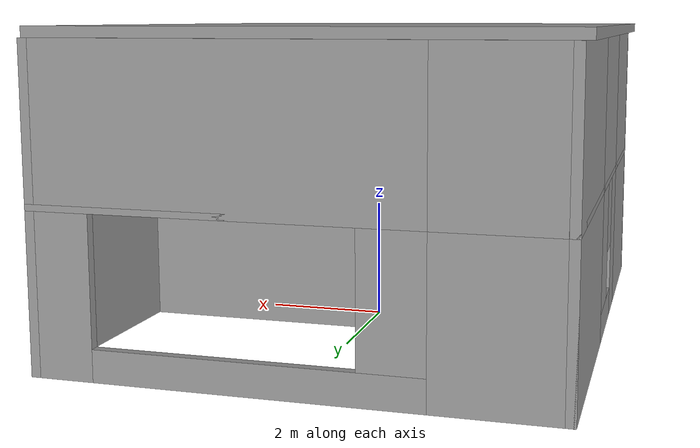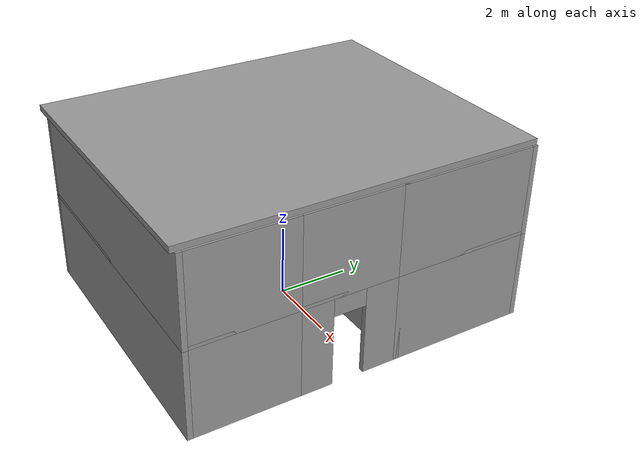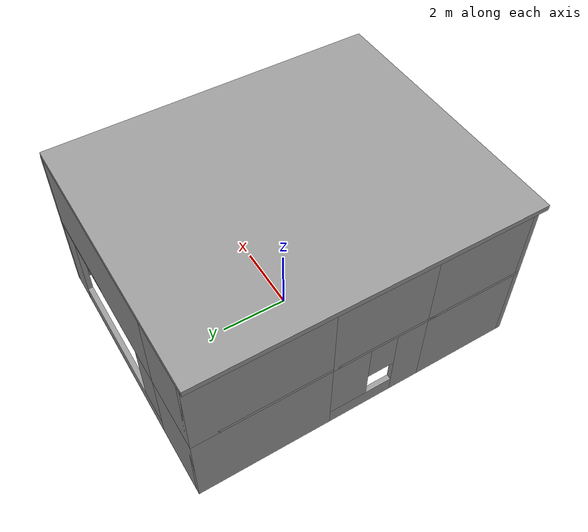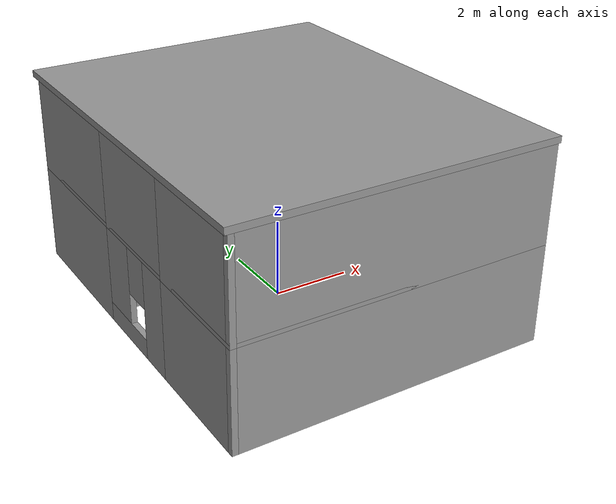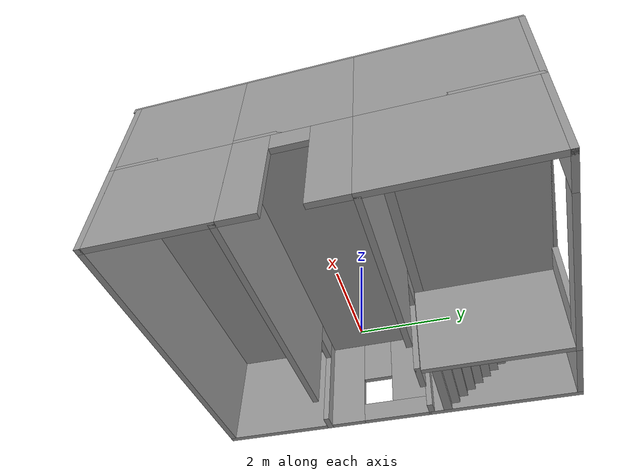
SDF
<?xml version='1.0'?>
<sdf version='1.6'>
  <model name='testbuilding'>
    <link name='Floor_0'>
      <pose frame=''>0 0 2.5 0 -0 0</pose>
      <self_collide>0</self_collide>
      <enable_wind>0</enable_wind>
      <kinematic>0</kinematic>
      <visual name='Floor_0_Visual_0'>
        <pose frame=''>-3.92368 0 0.05 0 -0 0</pose>
        <geometry>
          <box>
            <size>0.152649 9.7 0.1</size>
          </box>
        </geometry>
        <material>
          <script>
            <uri>file://media/materials/scripts/gazebo.material</uri>
            <name>Gazebo/Grey</name>
          </script>
          <ambient>1 1 1 1</ambient>
        </material>
        <meta>
          <layer>1</layer>
        </meta>
        <transparency>0</transparency>
        <cast_shadows>1</cast_shadows>
      </visual>
      <visual name='Floor_0_Visual_1'>
        <pose frame=''>0.076324 -1.8001 0.05 0 -0 0</pose>
        <geometry>
          <box>
            <size>7.84735 6.0998 0.1</size>
          </box>
        </geometry>
        <material>
          <script>
            <uri>file://media/materials/scripts/gazebo.material</uri>
            <name>Gazebo/Grey</name>
          </script>
          <ambient>1 1 1 1</ambient>
        </material>
        <meta>
          <layer>1</layer>
        </meta>
        <transparency>0</transparency>
        <cast_shadows>1</cast_shadows>
      </visual>
      <visual name='Floor_0_Visual_2'>
        <pose frame=''>1.00217 3.0499 0.05 0 -0 0</pose>
        <geometry>
          <box>
            <size>5.99566 3.6002 0.1</size>
          </box>
        </geometry>
        <material>
          <script>
            <uri>file://media/materials/scripts/gazebo.material</uri>
            <name>Gazebo/Grey</name>
          </script>
          <ambient>1 1 1 1</ambient>
        </material>
        <meta>
          <layer>1</layer>
        </meta>
        <transparency>0</transparency>
        <cast_shadows>1</cast_shadows>
      </visual>
      <visual name='Floor_0_Visual_3'>
        <pose frame=''>-2.92151 4.75618 0.05 0 -0 0</pose>
        <geometry>
          <box>
            <size>1.85169 0.187632 0.1</size>
          </box>
        </geometry>
        <material>
          <script>
            <uri>file://media/materials/scripts/gazebo.material</uri>
            <name>Gazebo/Grey</name>
          </script>
          <ambient>1 1 1 1</ambient>
        </material>
        <meta>
          <layer>1</layer>
        </meta>
        <transparency>0</transparency>
        <cast_shadows>1</cast_shadows>
      </visual>
      <collision name='Floor_0_Collision_0'>
        <laser_retro>0</laser_retro>
        <max_contacts>10</max_contacts>
        <pose frame=''>-3.92368 0 0.05 0 -0 0</pose>
        <geometry>
          <box>
            <size>0.152649 9.7 0.1</size>
          </box>
        </geometry>
        <surface>
          <friction>
            <ode>
              <mu>1</mu>
              <mu2>1</mu2>
              <fdir1>0 0 0</fdir1>
              <slip1>0</slip1>
              <slip2>0</slip2>
            </ode>
            <torsional>
              <coefficient>1</coefficient>
              <patch_radius>0</patch_radius>
              <surface_radius>0</surface_radius>
              <use_patch_radius>1</use_patch_radius>
              <ode>
                <slip>0</slip>
              </ode>
            </torsional>
          </friction>
          <bounce>
            <restitution_coefficient>0</restitution_coefficient>
            <threshold>1e+06</threshold>
          </bounce>
          <contact>
            <collide_without_contact>0</collide_without_contact>
            <collide_without_contact_bitmask>1</collide_without_contact_bitmask>
            <collide_bitmask>1</collide_bitmask>
            <ode>
              <soft_cfm>0</soft_cfm>
              <soft_erp>0.2</soft_erp>
              <kp>1e+13</kp>
              <kd>1</kd>
              <max_vel>0.01</max_vel>
              <min_depth>0</min_depth>
            </ode>
            <bullet>
              <split_impulse>1</split_impulse>
              <split_impulse_penetration_threshold>-0.01</split_impulse_penetration_threshold>
              <soft_cfm>0</soft_cfm>
              <soft_erp>0.2</soft_erp>
              <kp>1e+13</kp>
              <kd>1</kd>
            </bullet>
          </contact>
        </surface>
      </collision>
      <collision name='Floor_0_Collision_1'>
        <laser_retro>0</laser_retro>
        <max_contacts>10</max_contacts>
        <pose frame=''>0.076324 -1.8001 0.05 0 -0 0</pose>
        <geometry>
          <box>
            <size>7.84735 6.0998 0.1</size>
          </box>
        </geometry>
        <surface>
          <friction>
            <ode>
              <mu>1</mu>
              <mu2>1</mu2>
              <fdir1>0 0 0</fdir1>
              <slip1>0</slip1>
              <slip2>0</slip2>
            </ode>
            <torsional>
              <coefficient>1</coefficient>
              <patch_radius>0</patch_radius>
              <surface_radius>0</surface_radius>
              <use_patch_radius>1</use_patch_radius>
              <ode>
                <slip>0</slip>
              </ode>
            </torsional>
          </friction>
          <bounce>
            <restitution_coefficient>0</restitution_coefficient>
            <threshold>1e+06</threshold>
          </bounce>
          <contact>
            <collide_without_contact>0</collide_without_contact>
            <collide_without_contact_bitmask>1</collide_without_contact_bitmask>
            <collide_bitmask>1</collide_bitmask>
            <ode>
              <soft_cfm>0</soft_cfm>
              <soft_erp>0.2</soft_erp>
              <kp>1e+13</kp>
              <kd>1</kd>
              <max_vel>0.01</max_vel>
              <min_depth>0</min_depth>
            </ode>
            <bullet>
              <split_impulse>1</split_impulse>
              <split_impulse_penetration_threshold>-0.01</split_impulse_penetration_threshold>
              <soft_cfm>0</soft_cfm>
              <soft_erp>0.2</soft_erp>
              <kp>1e+13</kp>
              <kd>1</kd>
            </bullet>
          </contact>
        </surface>
      </collision>
      <collision name='Floor_0_Collision_2'>
        <laser_retro>0</laser_retro>
        <max_contacts>10</max_contacts>
        <pose frame=''>1.00217 3.0499 0.05 0 -0 0</pose>
        <geometry>
          <box>
            <size>5.99566 3.6002 0.1</size>
          </box>
        </geometry>
        <surface>
          <friction>
            <ode>
              <mu>1</mu>
              <mu2>1</mu2>
              <fdir1>0 0 0</fdir1>
              <slip1>0</slip1>
              <slip2>0</slip2>
            </ode>
            <torsional>
              <coefficient>1</coefficient>
              <patch_radius>0</patch_radius>
              <surface_radius>0</surface_radius>
              <use_patch_radius>1</use_patch_radius>
              <ode>
                <slip>0</slip>
              </ode>
            </torsional>
          </friction>
          <bounce>
            <restitution_coefficient>0</restitution_coefficient>
            <threshold>1e+06</threshold>
          </bounce>
          <contact>
            <collide_without_contact>0</collide_without_contact>
            <collide_without_contact_bitmask>1</collide_without_contact_bitmask>
            <collide_bitmask>1</collide_bitmask>
            <ode>
              <soft_cfm>0</soft_cfm>
              <soft_erp>0.2</soft_erp>
              <kp>1e+13</kp>
              <kd>1</kd>
              <max_vel>0.01</max_vel>
              <min_depth>0</min_depth>
            </ode>
            <bullet>
              <split_impulse>1</split_impulse>
              <split_impulse_penetration_threshold>-0.01</split_impulse_penetration_threshold>
              <soft_cfm>0</soft_cfm>
              <soft_erp>0.2</soft_erp>
              <kp>1e+13</kp>
              <kd>1</kd>
            </bullet>
          </contact>
        </surface>
      </collision>
      <collision name='Floor_0_Collision_3'>
        <laser_retro>0</laser_retro>
        <max_contacts>10</max_contacts>
        <pose frame=''>-2.92151 4.75618 0.05 0 -0 0</pose>
        <geometry>
          <box>
            <size>1.85169 0.187632 0.1</size>
          </box>
        </geometry>
        <surface>
          <friction>
            <ode>
              <mu>1</mu>
              <mu2>1</mu2>
              <fdir1>0 0 0</fdir1>
              <slip1>0</slip1>
              <slip2>0</slip2>
            </ode>
            <torsional>
              <coefficient>1</coefficient>
              <patch_radius>0</patch_radius>
              <surface_radius>0</surface_radius>
              <use_patch_radius>1</use_patch_radius>
              <ode>
                <slip>0</slip>
              </ode>
            </torsional>
          </friction>
          <bounce>
            <restitution_coefficient>0</restitution_coefficient>
            <threshold>1e+06</threshold>
          </bounce>
          <contact>
            <collide_without_contact>0</collide_without_contact>
            <collide_without_contact_bitmask>1</collide_without_contact_bitmask>
            <collide_bitmask>1</collide_bitmask>
            <ode>
              <soft_cfm>0</soft_cfm>
              <soft_erp>0.2</soft_erp>
              <kp>1e+13</kp>
              <kd>1</kd>
              <max_vel>0.01</max_vel>
              <min_depth>0</min_depth>
            </ode>
            <bullet>
              <split_impulse>1</split_impulse>
              <split_impulse_penetration_threshold>-0.01</split_impulse_penetration_threshold>
              <soft_cfm>0</soft_cfm>
              <soft_erp>0.2</soft_erp>
              <kp>1e+13</kp>
              <kd>1</kd>
            </bullet>
          </contact>
        </surface>
      </collision>
    </link>
    <link name='Stairs_1'>
      <self_collide>0</self_collide>
      <enable_wind>0</enable_wind>
      <kinematic>0</kinematic>
      <pose frame=''>0 0 0 0 -0 0</pose>
      <visual name='Stairs_1_Visual_6'>
        <pose frame=''>-2.92151 2.72858 1.08333 0 -0 -3.14159</pose>
        <geometry>
          <box>
            <size>1.85169 0.227504 0.166667</size>
          </box>
        </geometry>
        <material>
          <script>
            <uri>file://media/materials/scripts/gazebo.material</uri>
            <name>Gazebo/Grey</name>
          </script>
          <ambient>1 1 1 1</ambient>
        </material>
        <meta>
          <layer>0</layer>
        </meta>
        <transparency>0</transparency>
        <cast_shadows>1</cast_shadows>
      </visual>
      <visual name='Stairs_1_Visual_0'>
        <pose frame=''>-2.92151 1.36356 0.083333 0 -0 -3.14159</pose>
        <geometry>
          <box>
            <size>1.85169 0.227504 0.166667</size>
          </box>
        </geometry>
        <material>
          <script>
            <uri>file://media/materials/scripts/gazebo.material</uri>
            <name>Gazebo/Grey</name>
          </script>
          <ambient>1 1 1 1</ambient>
        </material>
        <meta>
          <layer>0</layer>
        </meta>
        <transparency>0</transparency>
        <cast_shadows>1</cast_shadows>
      </visual>
      <visual name='Stairs_1_Visual_1'>
        <pose frame=''>-2.92151 1.59106 0.25 0 -0 -3.14159</pose>
        <geometry>
          <box>
            <size>1.85169 0.227504 0.166667</size>
          </box>
        </geometry>
        <material>
          <script>
            <uri>file://media/materials/scripts/gazebo.material</uri>
            <name>Gazebo/Grey</name>
          </script>
          <ambient>1 1 1 1</ambient>
        </material>
        <meta>
          <layer>0</layer>
        </meta>
        <transparency>0</transparency>
        <cast_shadows>1</cast_shadows>
      </visual>
      <visual name='Stairs_1_Visual_2'>
        <pose frame=''>-2.92151 1.81856 0.416667 0 -0 -3.14159</pose>
        <geometry>
          <box>
            <size>1.85169 0.227504 0.166667</size>
          </box>
        </geometry>
        <material>
          <script>
            <uri>file://media/materials/scripts/gazebo.material</uri>
            <name>Gazebo/Grey</name>
          </script>
          <ambient>1 1 1 1</ambient>
        </material>
        <meta>
          <layer>0</layer>
        </meta>
        <transparency>0</transparency>
        <cast_shadows>1</cast_shadows>
      </visual>
      <visual name='Stairs_1_Visual_3'>
        <pose frame=''>-2.92151 2.04607 0.583333 0 -0 -3.14159</pose>
        <geometry>
          <box>
            <size>1.85169 0.227504 0.166667</size>
          </box>
        </geometry>
        <material>
          <script>
            <uri>file://media/materials/scripts/gazebo.material</uri>
            <name>Gazebo/Grey</name>
          </script>
          <ambient>1 1 1 1</ambient>
        </material>
        <meta>
          <layer>0</layer>
        </meta>
        <transparency>0</transparency>
        <cast_shadows>1</cast_shadows>
      </visual>
      <visual name='Stairs_1_Visual_4'>
        <pose frame=''>-2.92151 2.27357 0.75 0 -0 -3.14159</pose>
        <geometry>
          <box>
            <size>1.85169 0.227504 0.166667</size>
          </box>
        </geometry>
        <material>
          <script>
            <uri>file://media/materials/scripts/gazebo.material</uri>
            <name>Gazebo/Grey</name>
          </script>
          <ambient>1 1 1 1</ambient>
        </material>
        <meta>
          <layer>0</layer>
        </meta>
        <transparency>0</transparency>
        <cast_shadows>1</cast_shadows>
      </visual>
      <visual name='Stairs_1_Visual_5'>
        <pose frame=''>-2.92151 2.50108 0.916667 0 -0 -3.14159</pose>
        <geometry>
          <box>
            <size>1.85169 0.227504 0.166667</size>
          </box>
        </geometry>
        <material>
          <script>
            <uri>file://media/materials/scripts/gazebo.material</uri>
            <name>Gazebo/Grey</name>
          </script>
          <ambient>1 1 1 1</ambient>
        </material>
        <meta>
          <layer>0</layer>
        </meta>
        <transparency>0</transparency>
        <cast_shadows>1</cast_shadows>
      </visual>
      <visual name='Stairs_1_Visual_7'>
        <pose frame=''>-2.92151 2.95609 1.25 0 -0 -3.14159</pose>
        <geometry>
          <box>
            <size>1.85169 0.227504 0.166667</size>
          </box>
        </geometry>
        <material>
          <script>
            <uri>file://media/materials/scripts/gazebo.material</uri>
            <name>Gazebo/Grey</name>
          </script>
          <ambient>1 1 1 1</ambient>
        </material>
        <meta>
          <layer>0</layer>
        </meta>
        <transparency>0</transparency>
        <cast_shadows>1</cast_shadows>
      </visual>
      <visual name='Stairs_1_Visual_8'>
        <pose frame=''>-2.92151 3.18359 1.41667 0 -0 -3.14159</pose>
        <geometry>
          <box>
            <size>1.85169 0.227504 0.166667</size>
          </box>
        </geometry>
        <material>
          <script>
            <uri>file://media/materials/scripts/gazebo.material</uri>
            <name>Gazebo/Grey</name>
          </script>
          <ambient>1 1 1 1</ambient>
        </material>
        <meta>
          <layer>0</layer>
        </meta>
        <transparency>0</transparency>
        <cast_shadows>1</cast_shadows>
      </visual>
      <visual name='Stairs_1_Visual_9'>
        <pose frame=''>-2.92151 3.41109 1.58333 0 -0 -3.14159</pose>
        <geometry>
          <box>
            <size>1.85169 0.227504 0.166667</size>
          </box>
        </geometry>
        <material>
          <script>
            <uri>file://media/materials/scripts/gazebo.material</uri>
            <name>Gazebo/Grey</name>
          </script>
          <ambient>1 1 1 1</ambient>
        </material>
        <meta>
          <layer>0</layer>
        </meta>
        <transparency>0</transparency>
        <cast_shadows>1</cast_shadows>
      </visual>
      <visual name='Stairs_1_Visual_10'>
        <pose frame=''>-2.92151 3.6386 1.75 0 -0 -3.14159</pose>
        <geometry>
          <box>
            <size>1.85169 0.227504 0.166667</size>
          </box>
        </geometry>
        <material>
          <script>
            <uri>file://media/materials/scripts/gazebo.material</uri>
            <name>Gazebo/Grey</name>
          </script>
          <ambient>1 1 1 1</ambient>
        </material>
        <meta>
          <layer>0</layer>
        </meta>
        <transparency>0</transparency>
        <cast_shadows>1</cast_shadows>
      </visual>
      <visual name='Stairs_1_Visual_11'>
        <pose frame=''>-2.92151 3.8661 1.91667 0 -0 -3.14159</pose>
        <geometry>
          <box>
            <size>1.85169 0.227504 0.166667</size>
          </box>
        </geometry>
        <material>
          <script>
            <uri>file://media/materials/scripts/gazebo.material</uri>
            <name>Gazebo/Grey</name>
          </script>
          <ambient>1 1 1 1</ambient>
        </material>
        <meta>
          <layer>0</layer>
        </meta>
        <transparency>0</transparency>
        <cast_shadows>1</cast_shadows>
      </visual>
      <visual name='Stairs_1_Visual_12'>
        <pose frame=''>-2.92151 4.09361 2.08333 0 -0 -3.14159</pose>
        <geometry>
          <box>
            <size>1.85169 0.227504 0.166667</size>
          </box>
        </geometry>
        <material>
          <script>
            <uri>file://media/materials/scripts/gazebo.material</uri>
            <name>Gazebo/Grey</name>
          </script>
          <ambient>1 1 1 1</ambient>
        </material>
        <meta>
          <layer>0</layer>
        </meta>
        <transparency>0</transparency>
        <cast_shadows>1</cast_shadows>
      </visual>
      <visual name='Stairs_1_Visual_13'>
        <pose frame=''>-2.92151 4.32111 2.25 0 -0 -3.14159</pose>
        <geometry>
          <box>
            <size>1.85169 0.227504 0.166667</size>
          </box>
        </geometry>
        <material>
          <script>
            <uri>file://media/materials/scripts/gazebo.material</uri>
            <name>Gazebo/Grey</name>
          </script>
          <ambient>1 1 1 1</ambient>
        </material>
        <meta>
          <layer>0</layer>
        </meta>
        <transparency>0</transparency>
        <cast_shadows>1</cast_shadows>
      </visual>
      <visual name='Stairs_1_Visual_14'>
        <pose frame=''>-2.92151 4.54862 2.41667 0 -0 -3.14159</pose>
        <geometry>
          <box>
            <size>1.85169 0.227504 0.166667</size>
          </box>
        </geometry>
        <material>
          <script>
            <uri>file://media/materials/scripts/gazebo.material</uri>
            <name>Gazebo/Grey</name>
          </script>
          <ambient>1 1 1 1</ambient>
        </material>
        <meta>
          <layer>0</layer>
        </meta>
        <transparency>0</transparency>
        <cast_shadows>1</cast_shadows>
      </visual>
      <collision name='Stairs_1_Collision_0'>
        <laser_retro>0</laser_retro>
        <max_contacts>10</max_contacts>
        <pose frame=''>-2.92151 1.36356 0.083333 0 0 -3.14159</pose>
        <geometry>
          <box>
            <size>1.85169 0.227504 0.166667</size>
          </box>
        </geometry>
        <surface>
          <friction>
            <ode>
              <mu>1</mu>
              <mu2>1</mu2>
              <fdir1>0 0 0</fdir1>
              <slip1>0</slip1>
              <slip2>0</slip2>
            </ode>
            <torsional>
              <coefficient>1</coefficient>
              <patch_radius>0</patch_radius>
              <surface_radius>0</surface_radius>
              <use_patch_radius>1</use_patch_radius>
              <ode>
                <slip>0</slip>
              </ode>
            </torsional>
          </friction>
          <bounce>
            <restitution_coefficient>0</restitution_coefficient>
            <threshold>1e+06</threshold>
          </bounce>
          <contact>
            <collide_without_contact>0</collide_without_contact>
            <collide_without_contact_bitmask>1</collide_without_contact_bitmask>
            <collide_bitmask>1</collide_bitmask>
            <ode>
              <soft_cfm>0</soft_cfm>
              <soft_erp>0.2</soft_erp>
              <kp>1e+13</kp>
              <kd>1</kd>
              <max_vel>0.01</max_vel>
              <min_depth>0</min_depth>
            </ode>
            <bullet>
              <split_impulse>1</split_impulse>
              <split_impulse_penetration_threshold>-0.01</split_impulse_penetration_threshold>
              <soft_cfm>0</soft_cfm>
              <soft_erp>0.2</soft_erp>
              <kp>1e+13</kp>
              <kd>1</kd>
            </bullet>
          </contact>
        </surface>
      </collision>
      <collision name='Stairs_1_Collision_1'>
        <laser_retro>0</laser_retro>
        <max_contacts>10</max_contacts>
        <pose frame=''>-2.92151 1.59106 0.25 0 0 -3.14159</pose>
        <geometry>
          <box>
            <size>1.85169 0.227504 0.166667</size>
          </box>
        </geometry>
        <surface>
          <friction>
            <ode>
              <mu>1</mu>
              <mu2>1</mu2>
              <fdir1>0 0 0</fdir1>
              <slip1>0</slip1>
              <slip2>0</slip2>
            </ode>
            <torsional>
              <coefficient>1</coefficient>
              <patch_radius>0</patch_radius>
              <surface_radius>0</surface_radius>
              <use_patch_radius>1</use_patch_radius>
              <ode>
                <slip>0</slip>
              </ode>
            </torsional>
          </friction>
          <bounce>
            <restitution_coefficient>0</restitution_coefficient>
            <threshold>1e+06</threshold>
          </bounce>
          <contact>
            <collide_without_contact>0</collide_without_contact>
            <collide_without_contact_bitmask>1</collide_without_contact_bitmask>
            <collide_bitmask>1</collide_bitmask>
            <ode>
              <soft_cfm>0</soft_cfm>
              <soft_erp>0.2</soft_erp>
              <kp>1e+13</kp>
              <kd>1</kd>
              <max_vel>0.01</max_vel>
              <min_depth>0</min_depth>
            </ode>
            <bullet>
              <split_impulse>1</split_impulse>
              <split_impulse_penetration_threshold>-0.01</split_impulse_penetration_threshold>
              <soft_cfm>0</soft_cfm>
              <soft_erp>0.2</soft_erp>
              <kp>1e+13</kp>
              <kd>1</kd>
            </bullet>
          </contact>
        </surface>
      </collision>
      <collision name='Stairs_1_Collision_2'>
        <laser_retro>0</laser_retro>
        <max_contacts>10</max_contacts>
        <pose frame=''>-2.92151 1.81856 0.416667 0 0 -3.14159</pose>
        <geometry>
          <box>
            <size>1.85169 0.227504 0.166667</size>
          </box>
        </geometry>
        <surface>
          <friction>
            <ode>
              <mu>1</mu>
              <mu2>1</mu2>
              <fdir1>0 0 0</fdir1>
              <slip1>0</slip1>
              <slip2>0</slip2>
            </ode>
            <torsional>
              <coefficient>1</coefficient>
              <patch_radius>0</patch_radius>
              <surface_radius>0</surface_radius>
              <use_patch_radius>1</use_patch_radius>
              <ode>
                <slip>0</slip>
              </ode>
            </torsional>
          </friction>
          <bounce>
            <restitution_coefficient>0</restitution_coefficient>
            <threshold>1e+06</threshold>
          </bounce>
          <contact>
            <collide_without_contact>0</collide_without_contact>
            <collide_without_contact_bitmask>1</collide_without_contact_bitmask>
            <collide_bitmask>1</collide_bitmask>
            <ode>
              <soft_cfm>0</soft_cfm>
              <soft_erp>0.2</soft_erp>
              <kp>1e+13</kp>
              <kd>1</kd>
              <max_vel>0.01</max_vel>
              <min_depth>0</min_depth>
            </ode>
            <bullet>
              <split_impulse>1</split_impulse>
              <split_impulse_penetration_threshold>-0.01</split_impulse_penetration_threshold>
              <soft_cfm>0</soft_cfm>
              <soft_erp>0.2</soft_erp>
              <kp>1e+13</kp>
              <kd>1</kd>
            </bullet>
          </contact>
        </surface>
      </collision>
      <collision name='Stairs_1_Collision_3'>
        <laser_retro>0</laser_retro>
        <max_contacts>10</max_contacts>
        <pose frame=''>-2.92151 2.04607 0.583333 0 0 -3.14159</pose>
        <geometry>
          <box>
            <size>1.85169 0.227504 0.166667</size>
          </box>
        </geometry>
        <surface>
          <friction>
            <ode>
              <mu>1</mu>
              <mu2>1</mu2>
              <fdir1>0 0 0</fdir1>
              <slip1>0</slip1>
              <slip2>0</slip2>
            </ode>
            <torsional>
              <coefficient>1</coefficient>
              <patch_radius>0</patch_radius>
              <surface_radius>0</surface_radius>
              <use_patch_radius>1</use_patch_radius>
              <ode>
                <slip>0</slip>
              </ode>
            </torsional>
          </friction>
          <bounce>
            <restitution_coefficient>0</restitution_coefficient>
            <threshold>1e+06</threshold>
          </bounce>
          <contact>
            <collide_without_contact>0</collide_without_contact>
            <collide_without_contact_bitmask>1</collide_without_contact_bitmask>
            <collide_bitmask>1</collide_bitmask>
            <ode>
              <soft_cfm>0</soft_cfm>
              <soft_erp>0.2</soft_erp>
              <kp>1e+13</kp>
              <kd>1</kd>
              <max_vel>0.01</max_vel>
              <min_depth>0</min_depth>
            </ode>
            <bullet>
              <split_impulse>1</split_impulse>
              <split_impulse_penetration_threshold>-0.01</split_impulse_penetration_threshold>
              <soft_cfm>0</soft_cfm>
              <soft_erp>0.2</soft_erp>
              <kp>1e+13</kp>
              <kd>1</kd>
            </bullet>
          </contact>
        </surface>
      </collision>
      <collision name='Stairs_1_Collision_4'>
        <laser_retro>0</laser_retro>
        <max_contacts>10</max_contacts>
        <pose frame=''>-2.92151 2.27357 0.75 0 0 -3.14159</pose>
        <geometry>
          <box>
            <size>1.85169 0.227504 0.166667</size>
          </box>
        </geometry>
        <surface>
          <friction>
            <ode>
              <mu>1</mu>
              <mu2>1</mu2>
              <fdir1>0 0 0</fdir1>
              <slip1>0</slip1>
              <slip2>0</slip2>
            </ode>
            <torsional>
              <coefficient>1</coefficient>
              <patch_radius>0</patch_radius>
              <surface_radius>0</surface_radius>
              <use_patch_radius>1</use_patch_radius>
              <ode>
                <slip>0</slip>
              </ode>
            </torsional>
          </friction>
          <bounce>
            <restitution_coefficient>0</restitution_coefficient>
            <threshold>1e+06</threshold>
          </bounce>
          <contact>
            <collide_without_contact>0</collide_without_contact>
            <collide_without_contact_bitmask>1</collide_without_contact_bitmask>
            <collide_bitmask>1</collide_bitmask>
            <ode>
              <soft_cfm>0</soft_cfm>
              <soft_erp>0.2</soft_erp>
              <kp>1e+13</kp>
              <kd>1</kd>
              <max_vel>0.01</max_vel>
              <min_depth>0</min_depth>
            </ode>
            <bullet>
              <split_impulse>1</split_impulse>
              <split_impulse_penetration_threshold>-0.01</split_impulse_penetration_threshold>
              <soft_cfm>0</soft_cfm>
              <soft_erp>0.2</soft_erp>
              <kp>1e+13</kp>
              <kd>1</kd>
            </bullet>
          </contact>
        </surface>
      </collision>
      <collision name='Stairs_1_Collision_5'>
        <laser_retro>0</laser_retro>
        <max_contacts>10</max_contacts>
        <pose frame=''>-2.92151 2.50108 0.916667 0 0 -3.14159</pose>
        <geometry>
          <box>
            <size>1.85169 0.227504 0.166667</size>
          </box>
        </geometry>
        <surface>
          <friction>
            <ode>
              <mu>1</mu>
              <mu2>1</mu2>
              <fdir1>0 0 0</fdir1>
              <slip1>0</slip1>
              <slip2>0</slip2>
            </ode>
            <torsional>
              <coefficient>1</coefficient>
              <patch_radius>0</patch_radius>
              <surface_radius>0</surface_radius>
              <use_patch_radius>1</use_patch_radius>
              <ode>
                <slip>0</slip>
              </ode>
            </torsional>
          </friction>
          <bounce>
            <restitution_coefficient>0</restitution_coefficient>
            <threshold>1e+06</threshold>
          </bounce>
          <contact>
            <collide_without_contact>0</collide_without_contact>
            <collide_without_contact_bitmask>1</collide_without_contact_bitmask>
            <collide_bitmask>1</collide_bitmask>
            <ode>
              <soft_cfm>0</soft_cfm>
              <soft_erp>0.2</soft_erp>
              <kp>1e+13</kp>
              <kd>1</kd>
              <max_vel>0.01</max_vel>
              <min_depth>0</min_depth>
            </ode>
            <bullet>
              <split_impulse>1</split_impulse>
              <split_impulse_penetration_threshold>-0.01</split_impulse_penetration_threshold>
              <soft_cfm>0</soft_cfm>
              <soft_erp>0.2</soft_erp>
              <kp>1e+13</kp>
              <kd>1</kd>
            </bullet>
          </contact>
        </surface>
      </collision>
      <collision name='Stairs_1_Collision_6'>
        <laser_retro>0</laser_retro>
        <max_contacts>10</max_contacts>
        <pose frame=''>-2.92151 2.72858 1.08333 0 0 -3.14159</pose>
        <geometry>
          <box>
            <size>1.85169 0.227504 0.166667</size>
          </box>
        </geometry>
        <surface>
          <friction>
            <ode>
              <mu>1</mu>
              <mu2>1</mu2>
              <fdir1>0 0 0</fdir1>
              <slip1>0</slip1>
              <slip2>0</slip2>
            </ode>
            <torsional>
              <coefficient>1</coefficient>
              <patch_radius>0</patch_radius>
              <surface_radius>0</surface_radius>
              <use_patch_radius>1</use_patch_radius>
              <ode>
                <slip>0</slip>
              </ode>
            </torsional>
          </friction>
          <bounce>
            <restitution_coefficient>0</restitution_coefficient>
            <threshold>1e+06</threshold>
          </bounce>
          <contact>
            <collide_without_contact>0</collide_without_contact>
            <collide_without_contact_bitmask>1</collide_without_contact_bitmask>
            <collide_bitmask>1</collide_bitmask>
            <ode>
              <soft_cfm>0</soft_cfm>
              <soft_erp>0.2</soft_erp>
              <kp>1e+13</kp>
              <kd>1</kd>
              <max_vel>0.01</max_vel>
              <min_depth>0</min_depth>
            </ode>
            <bullet>
              <split_impulse>1</split_impulse>
              <split_impulse_penetration_threshold>-0.01</split_impulse_penetration_threshold>
              <soft_cfm>0</soft_cfm>
              <soft_erp>0.2</soft_erp>
              <kp>1e+13</kp>
              <kd>1</kd>
            </bullet>
          </contact>
        </surface>
      </collision>
      <collision name='Stairs_1_Collision_7'>
        <laser_retro>0</laser_retro>
        <max_contacts>10</max_contacts>
        <pose frame=''>-2.92151 2.95609 1.25 0 0 -3.14159</pose>
        <geometry>
          <box>
            <size>1.85169 0.227504 0.166667</size>
          </box>
        </geometry>
        <surface>
          <friction>
            <ode>
              <mu>1</mu>
              <mu2>1</mu2>
              <fdir1>0 0 0</fdir1>
              <slip1>0</slip1>
              <slip2>0</slip2>
            </ode>
            <torsional>
              <coefficient>1</coefficient>
              <patch_radius>0</patch_radius>
              <surface_radius>0</surface_radius>
              <use_patch_radius>1</use_patch_radius>
              <ode>
                <slip>0</slip>
              </ode>
            </torsional>
          </friction>
          <bounce>
            <restitution_coefficient>0</restitution_coefficient>
            <threshold>1e+06</threshold>
          </bounce>
          <contact>
            <collide_without_contact>0</collide_without_contact>
            <collide_without_contact_bitmask>1</collide_without_contact_bitmask>
            <collide_bitmask>1</collide_bitmask>
            <ode>
              <soft_cfm>0</soft_cfm>
              <soft_erp>0.2</soft_erp>
              <kp>1e+13</kp>
              <kd>1</kd>
              <max_vel>0.01</max_vel>
              <min_depth>0</min_depth>
            </ode>
            <bullet>
              <split_impulse>1</split_impulse>
              <split_impulse_penetration_threshold>-0.01</split_impulse_penetration_threshold>
              <soft_cfm>0</soft_cfm>
              <soft_erp>0.2</soft_erp>
              <kp>1e+13</kp>
              <kd>1</kd>
            </bullet>
          </contact>
        </surface>
      </collision>
      <collision name='Stairs_1_Collision_8'>
        <laser_retro>0</laser_retro>
        <max_contacts>10</max_contacts>
        <pose frame=''>-2.92151 3.18359 1.41667 0 0 -3.14159</pose>
        <geometry>
          <box>
            <size>1.85169 0.227504 0.166667</size>
          </box>
        </geometry>
        <surface>
          <friction>
            <ode>
              <mu>1</mu>
              <mu2>1</mu2>
              <fdir1>0 0 0</fdir1>
              <slip1>0</slip1>
              <slip2>0</slip2>
            </ode>
            <torsional>
              <coefficient>1</coefficient>
              <patch_radius>0</patch_radius>
              <surface_radius>0</surface_radius>
              <use_patch_radius>1</use_patch_radius>
              <ode>
                <slip>0</slip>
              </ode>
            </torsional>
          </friction>
          <bounce>
            <restitution_coefficient>0</restitution_coefficient>
            <threshold>1e+06</threshold>
          </bounce>
          <contact>
            <collide_without_contact>0</collide_without_contact>
            <collide_without_contact_bitmask>1</collide_without_contact_bitmask>
            <collide_bitmask>1</collide_bitmask>
            <ode>
              <soft_cfm>0</soft_cfm>
              <soft_erp>0.2</soft_erp>
              <kp>1e+13</kp>
              <kd>1</kd>
              <max_vel>0.01</max_vel>
              <min_depth>0</min_depth>
            </ode>
            <bullet>
              <split_impulse>1</split_impulse>
              <split_impulse_penetration_threshold>-0.01</split_impulse_penetration_threshold>
              <soft_cfm>0</soft_cfm>
              <soft_erp>0.2</soft_erp>
              <kp>1e+13</kp>
              <kd>1</kd>
            </bullet>
          </contact>
        </surface>
      </collision>
      <collision name='Stairs_1_Collision_9'>
        <laser_retro>0</laser_retro>
        <max_contacts>10</max_contacts>
        <pose frame=''>-2.92151 3.41109 1.58333 0 0 -3.14159</pose>
        <geometry>
          <box>
            <size>1.85169 0.227504 0.166667</size>
          </box>
        </geometry>
        <surface>
          <friction>
            <ode>
              <mu>1</mu>
              <mu2>1</mu2>
              <fdir1>0 0 0</fdir1>
              <slip1>0</slip1>
              <slip2>0</slip2>
            </ode>
            <torsional>
              <coefficient>1</coefficient>
              <patch_radius>0</patch_radius>
              <surface_radius>0</surface_radius>
              <use_patch_radius>1</use_patch_radius>
              <ode>
                <slip>0</slip>
              </ode>
            </torsional>
          </friction>
          <bounce>
            <restitution_coefficient>0</restitution_coefficient>
            <threshold>1e+06</threshold>
          </bounce>
          <contact>
            <collide_without_contact>0</collide_without_contact>
            <collide_without_contact_bitmask>1</collide_without_contact_bitmask>
            <collide_bitmask>1</collide_bitmask>
            <ode>
              <soft_cfm>0</soft_cfm>
              <soft_erp>0.2</soft_erp>
              <kp>1e+13</kp>
              <kd>1</kd>
              <max_vel>0.01</max_vel>
              <min_depth>0</min_depth>
            </ode>
            <bullet>
              <split_impulse>1</split_impulse>
              <split_impulse_penetration_threshold>-0.01</split_impulse_penetration_threshold>
              <soft_cfm>0</soft_cfm>
              <soft_erp>0.2</soft_erp>
              <kp>1e+13</kp>
              <kd>1</kd>
            </bullet>
          </contact>
        </surface>
      </collision>
      <collision name='Stairs_1_Collision_10'>
        <laser_retro>0</laser_retro>
        <max_contacts>10</max_contacts>
        <pose frame=''>-2.92151 3.6386 1.75 0 0 -3.14159</pose>
        <geometry>
          <box>
            <size>1.85169 0.227504 0.166667</size>
          </box>
        </geometry>
        <surface>
          <friction>
            <ode>
              <mu>1</mu>
              <mu2>1</mu2>
              <fdir1>0 0 0</fdir1>
              <slip1>0</slip1>
              <slip2>0</slip2>
            </ode>
            <torsional>
              <coefficient>1</coefficient>
              <patch_radius>0</patch_radius>
              <surface_radius>0</surface_radius>
              <use_patch_radius>1</use_patch_radius>
              <ode>
                <slip>0</slip>
              </ode>
            </torsional>
          </friction>
          <bounce>
            <restitution_coefficient>0</restitution_coefficient>
            <threshold>1e+06</threshold>
          </bounce>
          <contact>
            <collide_without_contact>0</collide_without_contact>
            <collide_without_contact_bitmask>1</collide_without_contact_bitmask>
            <collide_bitmask>1</collide_bitmask>
            <ode>
              <soft_cfm>0</soft_cfm>
              <soft_erp>0.2</soft_erp>
              <kp>1e+13</kp>
              <kd>1</kd>
              <max_vel>0.01</max_vel>
              <min_depth>0</min_depth>
            </ode>
            <bullet>
              <split_impulse>1</split_impulse>
              <split_impulse_penetration_threshold>-0.01</split_impulse_penetration_threshold>
              <soft_cfm>0</soft_cfm>
              <soft_erp>0.2</soft_erp>
              <kp>1e+13</kp>
              <kd>1</kd>
            </bullet>
          </contact>
        </surface>
      </collision>
      <collision name='Stairs_1_Collision_11'>
        <laser_retro>0</laser_retro>
        <max_contacts>10</max_contacts>
        <pose frame=''>-2.92151 3.8661 1.91667 0 0 -3.14159</pose>
        <geometry>
          <box>
            <size>1.85169 0.227504 0.166667</size>
          </box>
        </geometry>
        <surface>
          <friction>
            <ode>
              <mu>1</mu>
              <mu2>1</mu2>
              <fdir1>0 0 0</fdir1>
              <slip1>0</slip1>
              <slip2>0</slip2>
            </ode>
            <torsional>
              <coefficient>1</coefficient>
              <patch_radius>0</patch_radius>
              <surface_radius>0</surface_radius>
              <use_patch_radius>1</use_patch_radius>
              <ode>
                <slip>0</slip>
              </ode>
            </torsional>
          </friction>
          <bounce>
            <restitution_coefficient>0</restitution_coefficient>
            <threshold>1e+06</threshold>
          </bounce>
          <contact>
            <collide_without_contact>0</collide_without_contact>
            <collide_without_contact_bitmask>1</collide_without_contact_bitmask>
            <collide_bitmask>1</collide_bitmask>
            <ode>
              <soft_cfm>0</soft_cfm>
              <soft_erp>0.2</soft_erp>
              <kp>1e+13</kp>
              <kd>1</kd>
              <max_vel>0.01</max_vel>
              <min_depth>0</min_depth>
            </ode>
            <bullet>
              <split_impulse>1</split_impulse>
              <split_impulse_penetration_threshold>-0.01</split_impulse_penetration_threshold>
              <soft_cfm>0</soft_cfm>
              <soft_erp>0.2</soft_erp>
              <kp>1e+13</kp>
              <kd>1</kd>
            </bullet>
          </contact>
        </surface>
      </collision>
      <collision name='Stairs_1_Collision_12'>
        <laser_retro>0</laser_retro>
        <max_contacts>10</max_contacts>
        <pose frame=''>-2.92151 4.09361 2.08333 0 0 -3.14159</pose>
        <geometry>
          <box>
            <size>1.85169 0.227504 0.166667</size>
          </box>
        </geometry>
        <surface>
          <friction>
            <ode>
              <mu>1</mu>
              <mu2>1</mu2>
              <fdir1>0 0 0</fdir1>
              <slip1>0</slip1>
              <slip2>0</slip2>
            </ode>
            <torsional>
              <coefficient>1</coefficient>
              <patch_radius>0</patch_radius>
              <surface_radius>0</surface_radius>
              <use_patch_radius>1</use_patch_radius>
              <ode>
                <slip>0</slip>
              </ode>
            </torsional>
          </friction>
          <bounce>
            <restitution_coefficient>0</restitution_coefficient>
            <threshold>1e+06</threshold>
          </bounce>
          <contact>
            <collide_without_contact>0</collide_without_contact>
            <collide_without_contact_bitmask>1</collide_without_contact_bitmask>
            <collide_bitmask>1</collide_bitmask>
            <ode>
              <soft_cfm>0</soft_cfm>
              <soft_erp>0.2</soft_erp>
              <kp>1e+13</kp>
              <kd>1</kd>
              <max_vel>0.01</max_vel>
              <min_depth>0</min_depth>
            </ode>
            <bullet>
              <split_impulse>1</split_impulse>
              <split_impulse_penetration_threshold>-0.01</split_impulse_penetration_threshold>
              <soft_cfm>0</soft_cfm>
              <soft_erp>0.2</soft_erp>
              <kp>1e+13</kp>
              <kd>1</kd>
            </bullet>
          </contact>
        </surface>
      </collision>
      <collision name='Stairs_1_Collision_13'>
        <laser_retro>0</laser_retro>
        <max_contacts>10</max_contacts>
        <pose frame=''>-2.92151 4.32111 2.25 0 0 -3.14159</pose>
        <geometry>
          <box>
            <size>1.85169 0.227504 0.166667</size>
          </box>
        </geometry>
        <surface>
          <friction>
            <ode>
              <mu>1</mu>
              <mu2>1</mu2>
              <fdir1>0 0 0</fdir1>
              <slip1>0</slip1>
              <slip2>0</slip2>
            </ode>
            <torsional>
              <coefficient>1</coefficient>
              <patch_radius>0</patch_radius>
              <surface_radius>0</surface_radius>
              <use_patch_radius>1</use_patch_radius>
              <ode>
                <slip>0</slip>
              </ode>
            </torsional>
          </friction>
          <bounce>
            <restitution_coefficient>0</restitution_coefficient>
            <threshold>1e+06</threshold>
          </bounce>
          <contact>
            <collide_without_contact>0</collide_without_contact>
            <collide_without_contact_bitmask>1</collide_without_contact_bitmask>
            <collide_bitmask>1</collide_bitmask>
            <ode>
              <soft_cfm>0</soft_cfm>
              <soft_erp>0.2</soft_erp>
              <kp>1e+13</kp>
              <kd>1</kd>
              <max_vel>0.01</max_vel>
              <min_depth>0</min_depth>
            </ode>
            <bullet>
              <split_impulse>1</split_impulse>
              <split_impulse_penetration_threshold>-0.01</split_impulse_penetration_threshold>
              <soft_cfm>0</soft_cfm>
              <soft_erp>0.2</soft_erp>
              <kp>1e+13</kp>
              <kd>1</kd>
            </bullet>
          </contact>
        </surface>
      </collision>
      <collision name='Stairs_1_Collision_14'>
        <laser_retro>0</laser_retro>
        <max_contacts>10</max_contacts>
        <pose frame=''>-2.92151 4.54862 2.41667 0 0 -3.14159</pose>
        <geometry>
          <box>
            <size>1.85169 0.227504 0.166667</size>
          </box>
        </geometry>
        <surface>
          <friction>
            <ode>
              <mu>1</mu>
              <mu2>1</mu2>
              <fdir1>0 0 0</fdir1>
              <slip1>0</slip1>
              <slip2>0</slip2>
            </ode>
            <torsional>
              <coefficient>1</coefficient>
              <patch_radius>0</patch_radius>
              <surface_radius>0</surface_radius>
              <use_patch_radius>1</use_patch_radius>
              <ode>
                <slip>0</slip>
              </ode>
            </torsional>
          </friction>
          <bounce>
            <restitution_coefficient>0</restitution_coefficient>
            <threshold>1e+06</threshold>
          </bounce>
          <contact>
            <collide_without_contact>0</collide_without_contact>
            <collide_without_contact_bitmask>1</collide_without_contact_bitmask>
            <collide_bitmask>1</collide_bitmask>
            <ode>
              <soft_cfm>0</soft_cfm>
              <soft_erp>0.2</soft_erp>
              <kp>1e+13</kp>
              <kd>1</kd>
              <max_vel>0.01</max_vel>
              <min_depth>0</min_depth>
            </ode>
            <bullet>
              <split_impulse>1</split_impulse>
              <split_impulse_penetration_threshold>-0.01</split_impulse_penetration_threshold>
              <soft_cfm>0</soft_cfm>
              <soft_erp>0.2</soft_erp>
              <kp>1e+13</kp>
              <kd>1</kd>
            </bullet>
          </contact>
        </surface>
      </collision>
    </link>
    <link name='Wall_0'>
      <pose frame=''>0 0.925 0 0 -0 0</pose>
      <self_collide>0</self_collide>
      <enable_wind>0</enable_wind>
      <kinematic>0</kinematic>
      <visual name='Wall_0_Visual_0'>
        <pose frame=''>-3.75003 0 1.25 0 -0 0</pose>
        <geometry>
          <box>
            <size>0.499937 0.15 2.5</size>
          </box>
        </geometry>
        <material>
          <script>
            <uri>file://media/materials/scripts/gazebo.material</uri>
            <name>Gazebo/Grey</name>
          </script>
          <ambient>1 1 1 1</ambient>
        </material>
        <meta>
          <layer>0</layer>
        </meta>
        <transparency>0</transparency>
        <cast_shadows>1</cast_shadows>
      </visual>
      <visual name='Wall_0_Visual_1'>
        <pose frame=''>-2.17972 0 1.25 0 -0 0</pose>
        <geometry>
          <box>
            <size>0.840684 0.15 2.5</size>
          </box>
        </geometry>
        <material>
          <script>
            <uri>file://media/materials/scripts/gazebo.material</uri>
            <name>Gazebo/Grey</name>
          </script>
          <ambient>1 1 1 1</ambient>
        </material>
        <meta>
          <layer>0</layer>
        </meta>
        <transparency>0</transparency>
        <cast_shadows>1</cast_shadows>
      </visual>
      <visual name='Wall_0_Visual_2'>
        <pose frame=''>1.57031 0 1.25 0 -0 0</pose>
        <geometry>
          <box>
            <size>4.85938 0.15 2.5</size>
          </box>
        </geometry>
        <material>
          <script>
            <uri>file://media/materials/scripts/gazebo.material</uri>
            <name>Gazebo/Grey</name>
          </script>
          <ambient>1 1 1 1</ambient>
        </material>
        <meta>
          <layer>0</layer>
        </meta>
        <transparency>0</transparency>
        <cast_shadows>1</cast_shadows>
      </visual>
      <visual name='Wall_0_Visual_3'>
        <pose frame=''>-3.05006 0 2.25 0 -0 0</pose>
        <geometry>
          <box>
            <size>0.9 0.15 0.5</size>
          </box>
        </geometry>
        <material>
          <script>
            <uri>file://media/materials/scripts/gazebo.material</uri>
            <name>Gazebo/Grey</name>
          </script>
          <ambient>1 1 1 1</ambient>
        </material>
        <meta>
          <layer>0</layer>
        </meta>
        <transparency>0</transparency>
        <cast_shadows>1</cast_shadows>
      </visual>
      <visual name='Wall_0_Visual_4'>
        <pose frame=''>-1.30938 0 2.25 0 -0 0</pose>
        <geometry>
          <box>
            <size>0.9 0.15 0.5</size>
          </box>
        </geometry>
        <material>
          <script>
            <uri>file://media/materials/scripts/gazebo.material</uri>
            <name>Gazebo/Grey</name>
          </script>
          <ambient>1 1 1 1</ambient>
        </material>
        <meta>
          <layer>0</layer>
        </meta>
        <transparency>0</transparency>
        <cast_shadows>1</cast_shadows>
      </visual>
      <collision name='Wall_0_Collision_3'>
        <laser_retro>0</laser_retro>
        <max_contacts>10</max_contacts>
        <pose frame=''>-3.05006 0 2.25 0 -0 0</pose>
        <geometry>
          <box>
            <size>0.9 0.15 0.5</size>
          </box>
        </geometry>
        <surface>
          <friction>
            <ode>
              <mu>1</mu>
              <mu2>1</mu2>
              <fdir1>0 0 0</fdir1>
              <slip1>0</slip1>
              <slip2>0</slip2>
            </ode>
            <torsional>
              <coefficient>1</coefficient>
              <patch_radius>0</patch_radius>
              <surface_radius>0</surface_radius>
              <use_patch_radius>1</use_patch_radius>
              <ode>
                <slip>0</slip>
              </ode>
            </torsional>
          </friction>
          <bounce>
            <restitution_coefficient>0</restitution_coefficient>
            <threshold>1e+06</threshold>
          </bounce>
          <contact>
            <collide_without_contact>0</collide_without_contact>
            <collide_without_contact_bitmask>1</collide_without_contact_bitmask>
            <collide_bitmask>1</collide_bitmask>
            <ode>
              <soft_cfm>0</soft_cfm>
              <soft_erp>0.2</soft_erp>
              <kp>1e+13</kp>
              <kd>1</kd>
              <max_vel>0.01</max_vel>
              <min_depth>0</min_depth>
            </ode>
            <bullet>
              <split_impulse>1</split_impulse>
              <split_impulse_penetration_threshold>-0.01</split_impulse_penetration_threshold>
              <soft_cfm>0</soft_cfm>
              <soft_erp>0.2</soft_erp>
              <kp>1e+13</kp>
              <kd>1</kd>
            </bullet>
          </contact>
        </surface>
      </collision>
      <collision name='Wall_0_Collision_0'>
        <laser_retro>0</laser_retro>
        <max_contacts>10</max_contacts>
        <pose frame=''>-3.75003 0 1.25 0 -0 0</pose>
        <geometry>
          <box>
            <size>0.499937 0.15 2.5</size>
          </box>
        </geometry>
        <surface>
          <friction>
            <ode>
              <mu>1</mu>
              <mu2>1</mu2>
              <fdir1>0 0 0</fdir1>
              <slip1>0</slip1>
              <slip2>0</slip2>
            </ode>
            <torsional>
              <coefficient>1</coefficient>
              <patch_radius>0</patch_radius>
              <surface_radius>0</surface_radius>
              <use_patch_radius>1</use_patch_radius>
              <ode>
                <slip>0</slip>
              </ode>
            </torsional>
          </friction>
          <bounce>
            <restitution_coefficient>0</restitution_coefficient>
            <threshold>1e+06</threshold>
          </bounce>
          <contact>
            <collide_without_contact>0</collide_without_contact>
            <collide_without_contact_bitmask>1</collide_without_contact_bitmask>
            <collide_bitmask>1</collide_bitmask>
            <ode>
              <soft_cfm>0</soft_cfm>
              <soft_erp>0.2</soft_erp>
              <kp>1e+13</kp>
              <kd>1</kd>
              <max_vel>0.01</max_vel>
              <min_depth>0</min_depth>
            </ode>
            <bullet>
              <split_impulse>1</split_impulse>
              <split_impulse_penetration_threshold>-0.01</split_impulse_penetration_threshold>
              <soft_cfm>0</soft_cfm>
              <soft_erp>0.2</soft_erp>
              <kp>1e+13</kp>
              <kd>1</kd>
            </bullet>
          </contact>
        </surface>
      </collision>
      <collision name='Wall_0_Collision_1'>
        <laser_retro>0</laser_retro>
        <max_contacts>10</max_contacts>
        <pose frame=''>-2.17972 0 1.25 0 -0 0</pose>
        <geometry>
          <box>
            <size>0.840684 0.15 2.5</size>
          </box>
        </geometry>
        <surface>
          <friction>
            <ode>
              <mu>1</mu>
              <mu2>1</mu2>
              <fdir1>0 0 0</fdir1>
              <slip1>0</slip1>
              <slip2>0</slip2>
            </ode>
            <torsional>
              <coefficient>1</coefficient>
              <patch_radius>0</patch_radius>
              <surface_radius>0</surface_radius>
              <use_patch_radius>1</use_patch_radius>
              <ode>
                <slip>0</slip>
              </ode>
            </torsional>
          </friction>
          <bounce>
            <restitution_coefficient>0</restitution_coefficient>
            <threshold>1e+06</threshold>
          </bounce>
          <contact>
            <collide_without_contact>0</collide_without_contact>
            <collide_without_contact_bitmask>1</collide_without_contact_bitmask>
            <collide_bitmask>1</collide_bitmask>
            <ode>
              <soft_cfm>0</soft_cfm>
              <soft_erp>0.2</soft_erp>
              <kp>1e+13</kp>
              <kd>1</kd>
              <max_vel>0.01</max_vel>
              <min_depth>0</min_depth>
            </ode>
            <bullet>
              <split_impulse>1</split_impulse>
              <split_impulse_penetration_threshold>-0.01</split_impulse_penetration_threshold>
              <soft_cfm>0</soft_cfm>
              <soft_erp>0.2</soft_erp>
              <kp>1e+13</kp>
              <kd>1</kd>
            </bullet>
          </contact>
        </surface>
      </collision>
      <collision name='Wall_0_Collision_2'>
        <laser_retro>0</laser_retro>
        <max_contacts>10</max_contacts>
        <pose frame=''>1.57031 0 1.25 0 -0 0</pose>
        <geometry>
          <box>
            <size>4.85938 0.15 2.5</size>
          </box>
        </geometry>
        <surface>
          <friction>
            <ode>
              <mu>1</mu>
              <mu2>1</mu2>
              <fdir1>0 0 0</fdir1>
              <slip1>0</slip1>
              <slip2>0</slip2>
            </ode>
            <torsional>
              <coefficient>1</coefficient>
              <patch_radius>0</patch_radius>
              <surface_radius>0</surface_radius>
              <use_patch_radius>1</use_patch_radius>
              <ode>
                <slip>0</slip>
              </ode>
            </torsional>
          </friction>
          <bounce>
            <restitution_coefficient>0</restitution_coefficient>
            <threshold>1e+06</threshold>
          </bounce>
          <contact>
            <collide_without_contact>0</collide_without_contact>
            <collide_without_contact_bitmask>1</collide_without_contact_bitmask>
            <collide_bitmask>1</collide_bitmask>
            <ode>
              <soft_cfm>0</soft_cfm>
              <soft_erp>0.2</soft_erp>
              <kp>1e+13</kp>
              <kd>1</kd>
              <max_vel>0.01</max_vel>
              <min_depth>0</min_depth>
            </ode>
            <bullet>
              <split_impulse>1</split_impulse>
              <split_impulse_penetration_threshold>-0.01</split_impulse_penetration_threshold>
              <soft_cfm>0</soft_cfm>
              <soft_erp>0.2</soft_erp>
              <kp>1e+13</kp>
              <kd>1</kd>
            </bullet>
          </contact>
        </surface>
      </collision>
      <collision name='Wall_0_Collision_4'>
        <laser_retro>0</laser_retro>
        <max_contacts>10</max_contacts>
        <pose frame=''>-1.30938 0 2.25 0 -0 0</pose>
        <geometry>
          <box>
            <size>0.9 0.15 0.5</size>
          </box>
        </geometry>
        <surface>
          <friction>
            <ode>
              <mu>1</mu>
              <mu2>1</mu2>
              <fdir1>0 0 0</fdir1>
              <slip1>0</slip1>
              <slip2>0</slip2>
            </ode>
            <torsional>
              <coefficient>1</coefficient>
              <patch_radius>0</patch_radius>
              <surface_radius>0</surface_radius>
              <use_patch_radius>1</use_patch_radius>
              <ode>
                <slip>0</slip>
              </ode>
            </torsional>
          </friction>
          <bounce>
            <restitution_coefficient>0</restitution_coefficient>
            <threshold>1e+06</threshold>
          </bounce>
          <contact>
            <collide_without_contact>0</collide_without_contact>
            <collide_without_contact_bitmask>1</collide_without_contact_bitmask>
            <collide_bitmask>1</collide_bitmask>
            <ode>
              <soft_cfm>0</soft_cfm>
              <soft_erp>0.2</soft_erp>
              <kp>1e+13</kp>
              <kd>1</kd>
              <max_vel>0.01</max_vel>
              <min_depth>0</min_depth>
            </ode>
            <bullet>
              <split_impulse>1</split_impulse>
              <split_impulse_penetration_threshold>-0.01</split_impulse_penetration_threshold>
              <soft_cfm>0</soft_cfm>
              <soft_erp>0.2</soft_erp>
              <kp>1e+13</kp>
              <kd>1</kd>
            </bullet>
          </contact>
        </surface>
      </collision>
    </link>
    <link name='Wall_1'>
      <pose frame=''>3.925 -0.5 0 0 0 -1.5708</pose>
      <self_collide>0</self_collide>
      <enable_wind>0</enable_wind>
      <kinematic>0</kinematic>
      <visual name='Wall_1_Visual_0'>
        <pose frame=''>-0.962843 0 1.25 0 -0 0</pose>
        <geometry>
          <box>
            <size>1.07431 0.15 2.5</size>
          </box>
        </geometry>
        <material>
          <script>
            <uri>file://media/materials/scripts/gazebo.material</uri>
            <name>Gazebo/Grey</name>
          </script>
          <ambient>1 1 1 1</ambient>
        </material>
        <meta>
          <layer>0</layer>
        </meta>
        <transparency>0</transparency>
        <cast_shadows>1</cast_shadows>
      </visual>
      <visual name='Wall_1_Visual_1'>
        <pose frame=''>0.987157 0 1.25 0 -0 0</pose>
        <geometry>
          <box>
            <size>1.02569 0.15 2.5</size>
          </box>
        </geometry>
        <material>
          <script>
            <uri>file://media/materials/scripts/gazebo.material</uri>
            <name>Gazebo/Grey</name>
          </script>
          <ambient>1 1 1 1</ambient>
        </material>
        <meta>
          <layer>0</layer>
        </meta>
        <transparency>0</transparency>
        <cast_shadows>1</cast_shadows>
      </visual>
      <visual name='Wall_1_Visual_2'>
        <pose frame=''>0.024314 0 2.25 0 -0 0</pose>
        <geometry>
          <box>
            <size>0.9 0.15 0.5</size>
          </box>
        </geometry>
        <material>
          <script>
            <uri>file://media/materials/scripts/gazebo.material</uri>
            <name>Gazebo/Grey</name>
          </script>
          <ambient>1 1 1 1</ambient>
        </material>
        <meta>
          <layer>0</layer>
        </meta>
        <transparency>0</transparency>
        <cast_shadows>1</cast_shadows>
      </visual>
      <collision name='Wall_1_Collision_0'>
        <laser_retro>0</laser_retro>
        <max_contacts>10</max_contacts>
        <pose frame=''>-0.962843 0 1.25 0 -0 0</pose>
        <geometry>
          <box>
            <size>1.07431 0.15 2.5</size>
          </box>
        </geometry>
        <surface>
          <friction>
            <ode>
              <mu>1</mu>
              <mu2>1</mu2>
              <fdir1>0 0 0</fdir1>
              <slip1>0</slip1>
              <slip2>0</slip2>
            </ode>
            <torsional>
              <coefficient>1</coefficient>
              <patch_radius>0</patch_radius>
              <surface_radius>0</surface_radius>
              <use_patch_radius>1</use_patch_radius>
              <ode>
                <slip>0</slip>
              </ode>
            </torsional>
          </friction>
          <bounce>
            <restitution_coefficient>0</restitution_coefficient>
            <threshold>1e+06</threshold>
          </bounce>
          <contact>
            <collide_without_contact>0</collide_without_contact>
            <collide_without_contact_bitmask>1</collide_without_contact_bitmask>
            <collide_bitmask>1</collide_bitmask>
            <ode>
              <soft_cfm>0</soft_cfm>
              <soft_erp>0.2</soft_erp>
              <kp>1e+13</kp>
              <kd>1</kd>
              <max_vel>0.01</max_vel>
              <min_depth>0</min_depth>
            </ode>
            <bullet>
              <split_impulse>1</split_impulse>
              <split_impulse_penetration_threshold>-0.01</split_impulse_penetration_threshold>
              <soft_cfm>0</soft_cfm>
              <soft_erp>0.2</soft_erp>
              <kp>1e+13</kp>
              <kd>1</kd>
            </bullet>
          </contact>
        </surface>
      </collision>
      <collision name='Wall_1_Collision_1'>
        <laser_retro>0</laser_retro>
        <max_contacts>10</max_contacts>
        <pose frame=''>0.987157 0 1.25 0 -0 0</pose>
        <geometry>
          <box>
            <size>1.02569 0.15 2.5</size>
          </box>
        </geometry>
        <surface>
          <friction>
            <ode>
              <mu>1</mu>
              <mu2>1</mu2>
              <fdir1>0 0 0</fdir1>
              <slip1>0</slip1>
              <slip2>0</slip2>
            </ode>
            <torsional>
              <coefficient>1</coefficient>
              <patch_radius>0</patch_radius>
              <surface_radius>0</surface_radius>
              <use_patch_radius>1</use_patch_radius>
              <ode>
                <slip>0</slip>
              </ode>
            </torsional>
          </friction>
          <bounce>
            <restitution_coefficient>0</restitution_coefficient>
            <threshold>1e+06</threshold>
          </bounce>
          <contact>
            <collide_without_contact>0</collide_without_contact>
            <collide_without_contact_bitmask>1</collide_without_contact_bitmask>
            <collide_bitmask>1</collide_bitmask>
            <ode>
              <soft_cfm>0</soft_cfm>
              <soft_erp>0.2</soft_erp>
              <kp>1e+13</kp>
              <kd>1</kd>
              <max_vel>0.01</max_vel>
              <min_depth>0</min_depth>
            </ode>
            <bullet>
              <split_impulse>1</split_impulse>
              <split_impulse_penetration_threshold>-0.01</split_impulse_penetration_threshold>
              <soft_cfm>0</soft_cfm>
              <soft_erp>0.2</soft_erp>
              <kp>1e+13</kp>
              <kd>1</kd>
            </bullet>
          </contact>
        </surface>
      </collision>
      <collision name='Wall_1_Collision_2'>
        <laser_retro>0</laser_retro>
        <max_contacts>10</max_contacts>
        <pose frame=''>0.024314 0 2.25 0 -0 0</pose>
        <geometry>
          <box>
            <size>0.9 0.15 0.5</size>
          </box>
        </geometry>
        <surface>
          <friction>
            <ode>
              <mu>1</mu>
              <mu2>1</mu2>
              <fdir1>0 0 0</fdir1>
              <slip1>0</slip1>
              <slip2>0</slip2>
            </ode>
            <torsional>
              <coefficient>1</coefficient>
              <patch_radius>0</patch_radius>
              <surface_radius>0</surface_radius>
              <use_patch_radius>1</use_patch_radius>
              <ode>
                <slip>0</slip>
              </ode>
            </torsional>
          </friction>
          <bounce>
            <restitution_coefficient>0</restitution_coefficient>
            <threshold>1e+06</threshold>
          </bounce>
          <contact>
            <collide_without_contact>0</collide_without_contact>
            <collide_without_contact_bitmask>1</collide_without_contact_bitmask>
            <collide_bitmask>1</collide_bitmask>
            <ode>
              <soft_cfm>0</soft_cfm>
              <soft_erp>0.2</soft_erp>
              <kp>1e+13</kp>
              <kd>1</kd>
              <max_vel>0.01</max_vel>
              <min_depth>0</min_depth>
            </ode>
            <bullet>
              <split_impulse>1</split_impulse>
              <split_impulse_penetration_threshold>-0.01</split_impulse_penetration_threshold>
              <soft_cfm>0</soft_cfm>
              <soft_erp>0.2</soft_erp>
              <kp>1e+13</kp>
              <kd>1</kd>
            </bullet>
          </contact>
        </surface>
      </collision>
    </link>
    <link name='Wall_13'>
      <pose frame=''>-3.925 2.85 0 0 -0 1.5708</pose>
      <self_collide>0</self_collide>
      <enable_wind>0</enable_wind>
      <kinematic>0</kinematic>
      <visual name='Wall_13_Visual'>
        <pose frame=''>0 0 1.25 0 -0 0</pose>
        <geometry>
          <box>
            <size>4 0.15 2.5</size>
          </box>
        </geometry>
        <material>
          <script>
            <uri>file://media/materials/scripts/gazebo.material</uri>
            <name>Gazebo/Grey</name>
          </script>
          <ambient>1 1 1 1</ambient>
        </material>
        <meta>
          <layer>0</layer>
        </meta>
        <transparency>0</transparency>
        <cast_shadows>1</cast_shadows>
      </visual>
      <collision name='Wall_13_Collision'>
        <laser_retro>0</laser_retro>
        <max_contacts>10</max_contacts>
        <pose frame=''>0 0 1.25 0 -0 0</pose>
        <geometry>
          <box>
            <size>4 0.15 2.5</size>
          </box>
        </geometry>
        <surface>
          <friction>
            <ode>
              <mu>1</mu>
              <mu2>1</mu2>
              <fdir1>0 0 0</fdir1>
              <slip1>0</slip1>
              <slip2>0</slip2>
            </ode>
            <torsional>
              <coefficient>1</coefficient>
              <patch_radius>0</patch_radius>
              <surface_radius>0</surface_radius>
              <use_patch_radius>1</use_patch_radius>
              <ode>
                <slip>0</slip>
              </ode>
            </torsional>
          </friction>
          <bounce>
            <restitution_coefficient>0</restitution_coefficient>
            <threshold>1e+06</threshold>
          </bounce>
          <contact>
            <collide_without_contact>0</collide_without_contact>
            <collide_without_contact_bitmask>1</collide_without_contact_bitmask>
            <collide_bitmask>1</collide_bitmask>
            <ode>
              <soft_cfm>0</soft_cfm>
              <soft_erp>0.2</soft_erp>
              <kp>1e+13</kp>
              <kd>1</kd>
              <max_vel>0.01</max_vel>
              <min_depth>0</min_depth>
            </ode>
            <bullet>
              <split_impulse>1</split_impulse>
              <split_impulse_penetration_threshold>-0.01</split_impulse_penetration_threshold>
              <soft_cfm>0</soft_cfm>
              <soft_erp>0.2</soft_erp>
              <kp>1e+13</kp>
              <kd>1</kd>
            </bullet>
          </contact>
        </surface>
      </collision>
    </link>
    <link name='Wall_15'>
      <pose frame=''>-2.925 4.775 0 0 -0 0</pose>
      <self_collide>0</self_collide>
      <enable_wind>0</enable_wind>
      <kinematic>0</kinematic>
      <visual name='Wall_15_Visual'>
        <pose frame=''>0 0 1.25 0 -0 0</pose>
        <geometry>
          <box>
            <size>2.15 0.15 2.5</size>
          </box>
        </geometry>
        <material>
          <script>
            <uri>file://media/materials/scripts/gazebo.material</uri>
            <name>Gazebo/Grey</name>
          </script>
          <ambient>1 1 1 1</ambient>
        </material>
        <meta>
          <layer>0</layer>
        </meta>
        <transparency>0</transparency>
        <cast_shadows>1</cast_shadows>
      </visual>
      <collision name='Wall_15_Collision'>
        <laser_retro>0</laser_retro>
        <max_contacts>10</max_contacts>
        <pose frame=''>0 0 1.25 0 -0 0</pose>
        <geometry>
          <box>
            <size>2.15 0.15 2.5</size>
          </box>
        </geometry>
        <surface>
          <friction>
            <ode>
              <mu>1</mu>
              <mu2>1</mu2>
              <fdir1>0 0 0</fdir1>
              <slip1>0</slip1>
              <slip2>0</slip2>
            </ode>
            <torsional>
              <coefficient>1</coefficient>
              <patch_radius>0</patch_radius>
              <surface_radius>0</surface_radius>
              <use_patch_radius>1</use_patch_radius>
              <ode>
                <slip>0</slip>
              </ode>
            </torsional>
          </friction>
          <bounce>
            <restitution_coefficient>0</restitution_coefficient>
            <threshold>1e+06</threshold>
          </bounce>
          <contact>
            <collide_without_contact>0</collide_without_contact>
            <collide_without_contact_bitmask>1</collide_without_contact_bitmask>
            <collide_bitmask>1</collide_bitmask>
            <ode>
              <soft_cfm>0</soft_cfm>
              <soft_erp>0.2</soft_erp>
              <kp>1e+13</kp>
              <kd>1</kd>
              <max_vel>0.01</max_vel>
              <min_depth>0</min_depth>
            </ode>
            <bullet>
              <split_impulse>1</split_impulse>
              <split_impulse_penetration_threshold>-0.01</split_impulse_penetration_threshold>
              <soft_cfm>0</soft_cfm>
              <soft_erp>0.2</soft_erp>
              <kp>1e+13</kp>
              <kd>1</kd>
            </bullet>
          </contact>
        </surface>
      </collision>
    </link>
    <link name='Wall_17'>
      <pose frame=''>3.925 -3.35 0 0 0 -1.5708</pose>
      <self_collide>0</self_collide>
      <enable_wind>0</enable_wind>
      <kinematic>0</kinematic>
      <visual name='Wall_17_Visual'>
        <pose frame=''>0 0 1.25 0 -0 0</pose>
        <geometry>
          <box>
            <size>3 0.15 2.5</size>
          </box>
        </geometry>
        <material>
          <script>
            <uri>file://media/materials/scripts/gazebo.material</uri>
            <name>Gazebo/Grey</name>
          </script>
          <ambient>1 1 1 1</ambient>
        </material>
        <meta>
          <layer>0</layer>
        </meta>
        <transparency>0</transparency>
        <cast_shadows>1</cast_shadows>
      </visual>
      <collision name='Wall_17_Collision'>
        <laser_retro>0</laser_retro>
        <max_contacts>10</max_contacts>
        <pose frame=''>0 0 1.25 0 -0 0</pose>
        <geometry>
          <box>
            <size>3 0.15 2.5</size>
          </box>
        </geometry>
        <surface>
          <friction>
            <ode>
              <mu>1</mu>
              <mu2>1</mu2>
              <fdir1>0 0 0</fdir1>
              <slip1>0</slip1>
              <slip2>0</slip2>
            </ode>
            <torsional>
              <coefficient>1</coefficient>
              <patch_radius>0</patch_radius>
              <surface_radius>0</surface_radius>
              <use_patch_radius>1</use_patch_radius>
              <ode>
                <slip>0</slip>
              </ode>
            </torsional>
          </friction>
          <bounce>
            <restitution_coefficient>0</restitution_coefficient>
            <threshold>1e+06</threshold>
          </bounce>
          <contact>
            <collide_without_contact>0</collide_without_contact>
            <collide_without_contact_bitmask>1</collide_without_contact_bitmask>
            <collide_bitmask>1</collide_bitmask>
            <ode>
              <soft_cfm>0</soft_cfm>
              <soft_erp>0.2</soft_erp>
              <kp>1e+13</kp>
              <kd>1</kd>
              <max_vel>0.01</max_vel>
              <min_depth>0</min_depth>
            </ode>
            <bullet>
              <split_impulse>1</split_impulse>
              <split_impulse_penetration_threshold>-0.01</split_impulse_penetration_threshold>
              <soft_cfm>0</soft_cfm>
              <soft_erp>0.2</soft_erp>
              <kp>1e+13</kp>
              <kd>1</kd>
            </bullet>
          </contact>
        </surface>
      </collision>
    </link>
    <link name='Wall_18'>
      <pose frame=''>0 -4.775 0 0 -0 3.14159</pose>
      <self_collide>0</self_collide>
      <enable_wind>0</enable_wind>
      <kinematic>0</kinematic>
      <visual name='Wall_18_Visual'>
        <pose frame=''>0 0 1.25 0 -0 0</pose>
        <geometry>
          <box>
            <size>8 0.15 2.5</size>
          </box>
        </geometry>
        <material>
          <script>
            <uri>file://media/materials/scripts/gazebo.material</uri>
            <name>Gazebo/Grey</name>
          </script>
          <ambient>1 1 1 1</ambient>
        </material>
        <meta>
          <layer>0</layer>
        </meta>
        <transparency>0</transparency>
        <cast_shadows>1</cast_shadows>
      </visual>
      <collision name='Wall_18_Collision'>
        <laser_retro>0</laser_retro>
        <max_contacts>10</max_contacts>
        <pose frame=''>0 0 1.25 0 -0 0</pose>
        <geometry>
          <box>
            <size>8 0.15 2.5</size>
          </box>
        </geometry>
        <surface>
          <friction>
            <ode>
              <mu>1</mu>
              <mu2>1</mu2>
              <fdir1>0 0 0</fdir1>
              <slip1>0</slip1>
              <slip2>0</slip2>
            </ode>
            <torsional>
              <coefficient>1</coefficient>
              <patch_radius>0</patch_radius>
              <surface_radius>0</surface_radius>
              <use_patch_radius>1</use_patch_radius>
              <ode>
                <slip>0</slip>
              </ode>
            </torsional>
          </friction>
          <bounce>
            <restitution_coefficient>0</restitution_coefficient>
            <threshold>1e+06</threshold>
          </bounce>
          <contact>
            <collide_without_contact>0</collide_without_contact>
            <collide_without_contact_bitmask>1</collide_without_contact_bitmask>
            <collide_bitmask>1</collide_bitmask>
            <ode>
              <soft_cfm>0</soft_cfm>
              <soft_erp>0.2</soft_erp>
              <kp>1e+13</kp>
              <kd>1</kd>
              <max_vel>0.01</max_vel>
              <min_depth>0</min_depth>
            </ode>
            <bullet>
              <split_impulse>1</split_impulse>
              <split_impulse_penetration_threshold>-0.01</split_impulse_penetration_threshold>
              <soft_cfm>0</soft_cfm>
              <soft_erp>0.2</soft_erp>
              <kp>1e+13</kp>
              <kd>1</kd>
            </bullet>
          </contact>
        </surface>
      </collision>
    </link>
    <link name='Wall_19'>
      <pose frame=''>-3.925 -3.35 0 0 -0 1.5708</pose>
      <self_collide>0</self_collide>
      <enable_wind>0</enable_wind>
      <kinematic>0</kinematic>
      <visual name='Wall_19_Visual'>
        <pose frame=''>0 0 1.25 0 -0 0</pose>
        <geometry>
          <box>
            <size>3 0.15 2.5</size>
          </box>
        </geometry>
        <material>
          <script>
            <uri>file://media/materials/scripts/gazebo.material</uri>
            <name>Gazebo/Grey</name>
          </script>
          <ambient>1 1 1 1</ambient>
        </material>
        <meta>
          <layer>0</layer>
        </meta>
        <transparency>0</transparency>
        <cast_shadows>1</cast_shadows>
      </visual>
      <collision name='Wall_19_Collision'>
        <laser_retro>0</laser_retro>
        <max_contacts>10</max_contacts>
        <pose frame=''>0 0 1.25 0 -0 0</pose>
        <geometry>
          <box>
            <size>3 0.15 2.5</size>
          </box>
        </geometry>
        <surface>
          <friction>
            <ode>
              <mu>1</mu>
              <mu2>1</mu2>
              <fdir1>0 0 0</fdir1>
              <slip1>0</slip1>
              <slip2>0</slip2>
            </ode>
            <torsional>
              <coefficient>1</coefficient>
              <patch_radius>0</patch_radius>
              <surface_radius>0</surface_radius>
              <use_patch_radius>1</use_patch_radius>
              <ode>
                <slip>0</slip>
              </ode>
            </torsional>
          </friction>
          <bounce>
            <restitution_coefficient>0</restitution_coefficient>
            <threshold>1e+06</threshold>
          </bounce>
          <contact>
            <collide_without_contact>0</collide_without_contact>
            <collide_without_contact_bitmask>1</collide_without_contact_bitmask>
            <collide_bitmask>1</collide_bitmask>
            <ode>
              <soft_cfm>0</soft_cfm>
              <soft_erp>0.2</soft_erp>
              <kp>1e+13</kp>
              <kd>1</kd>
              <max_vel>0.01</max_vel>
              <min_depth>0</min_depth>
            </ode>
            <bullet>
              <split_impulse>1</split_impulse>
              <split_impulse_penetration_threshold>-0.01</split_impulse_penetration_threshold>
              <soft_cfm>0</soft_cfm>
              <soft_erp>0.2</soft_erp>
              <kp>1e+13</kp>
              <kd>1</kd>
            </bullet>
          </contact>
        </surface>
      </collision>
    </link>
    <link name='Wall_2'>
      <pose frame=''>0 -1.925 0 0 -0 3.14159</pose>
      <self_collide>0</self_collide>
      <enable_wind>0</enable_wind>
      <kinematic>0</kinematic>
      <visual name='Wall_2_Visual_0'>
        <pose frame=''>-0.699968 0 1.25 0 -0 0</pose>
        <geometry>
          <box>
            <size>6.60006 0.15 2.5</size>
          </box>
        </geometry>
        <material>
          <script>
            <uri>file://media/materials/scripts/gazebo.material</uri>
            <name>Gazebo/Grey</name>
          </script>
          <ambient>1 1 1 1</ambient>
        </material>
        <meta>
          <layer>0</layer>
        </meta>
        <transparency>0</transparency>
        <cast_shadows>1</cast_shadows>
      </visual>
      <visual name='Wall_2_Visual_1'>
        <pose frame=''>3.75003 0 1.25 0 -0 0</pose>
        <geometry>
          <box>
            <size>0.499937 0.15 2.5</size>
          </box>
        </geometry>
        <material>
          <script>
            <uri>file://media/materials/scripts/gazebo.material</uri>
            <name>Gazebo/Grey</name>
          </script>
          <ambient>1 1 1 1</ambient>
        </material>
        <meta>
          <layer>0</layer>
        </meta>
        <transparency>0</transparency>
        <cast_shadows>1</cast_shadows>
      </visual>
      <visual name='Wall_2_Visual_2'>
        <pose frame=''>3.05006 0 2.25 0 -0 0</pose>
        <geometry>
          <box>
            <size>0.9 0.15 0.5</size>
          </box>
        </geometry>
        <material>
          <script>
            <uri>file://media/materials/scripts/gazebo.material</uri>
            <name>Gazebo/Grey</name>
          </script>
          <ambient>1 1 1 1</ambient>
        </material>
        <meta>
          <layer>0</layer>
        </meta>
        <transparency>0</transparency>
        <cast_shadows>1</cast_shadows>
      </visual>
      <collision name='Wall_2_Collision_0'>
        <laser_retro>0</laser_retro>
        <max_contacts>10</max_contacts>
        <pose frame=''>-0.699968 0 1.25 0 -0 0</pose>
        <geometry>
          <box>
            <size>6.60006 0.15 2.5</size>
          </box>
        </geometry>
        <surface>
          <friction>
            <ode>
              <mu>1</mu>
              <mu2>1</mu2>
              <fdir1>0 0 0</fdir1>
              <slip1>0</slip1>
              <slip2>0</slip2>
            </ode>
            <torsional>
              <coefficient>1</coefficient>
              <patch_radius>0</patch_radius>
              <surface_radius>0</surface_radius>
              <use_patch_radius>1</use_patch_radius>
              <ode>
                <slip>0</slip>
              </ode>
            </torsional>
          </friction>
          <bounce>
            <restitution_coefficient>0</restitution_coefficient>
            <threshold>1e+06</threshold>
          </bounce>
          <contact>
            <collide_without_contact>0</collide_without_contact>
            <collide_without_contact_bitmask>1</collide_without_contact_bitmask>
            <collide_bitmask>1</collide_bitmask>
            <ode>
              <soft_cfm>0</soft_cfm>
              <soft_erp>0.2</soft_erp>
              <kp>1e+13</kp>
              <kd>1</kd>
              <max_vel>0.01</max_vel>
              <min_depth>0</min_depth>
            </ode>
            <bullet>
              <split_impulse>1</split_impulse>
              <split_impulse_penetration_threshold>-0.01</split_impulse_penetration_threshold>
              <soft_cfm>0</soft_cfm>
              <soft_erp>0.2</soft_erp>
              <kp>1e+13</kp>
              <kd>1</kd>
            </bullet>
          </contact>
        </surface>
      </collision>
      <collision name='Wall_2_Collision_1'>
        <laser_retro>0</laser_retro>
        <max_contacts>10</max_contacts>
        <pose frame=''>3.75003 0 1.25 0 -0 0</pose>
        <geometry>
          <box>
            <size>0.499937 0.15 2.5</size>
          </box>
        </geometry>
        <surface>
          <friction>
            <ode>
              <mu>1</mu>
              <mu2>1</mu2>
              <fdir1>0 0 0</fdir1>
              <slip1>0</slip1>
              <slip2>0</slip2>
            </ode>
            <torsional>
              <coefficient>1</coefficient>
              <patch_radius>0</patch_radius>
              <surface_radius>0</surface_radius>
              <use_patch_radius>1</use_patch_radius>
              <ode>
                <slip>0</slip>
              </ode>
            </torsional>
          </friction>
          <bounce>
            <restitution_coefficient>0</restitution_coefficient>
            <threshold>1e+06</threshold>
          </bounce>
          <contact>
            <collide_without_contact>0</collide_without_contact>
            <collide_without_contact_bitmask>1</collide_without_contact_bitmask>
            <collide_bitmask>1</collide_bitmask>
            <ode>
              <soft_cfm>0</soft_cfm>
              <soft_erp>0.2</soft_erp>
              <kp>1e+13</kp>
              <kd>1</kd>
              <max_vel>0.01</max_vel>
              <min_depth>0</min_depth>
            </ode>
            <bullet>
              <split_impulse>1</split_impulse>
              <split_impulse_penetration_threshold>-0.01</split_impulse_penetration_threshold>
              <soft_cfm>0</soft_cfm>
              <soft_erp>0.2</soft_erp>
              <kp>1e+13</kp>
              <kd>1</kd>
            </bullet>
          </contact>
        </surface>
      </collision>
      <collision name='Wall_2_Collision_2'>
        <laser_retro>0</laser_retro>
        <max_contacts>10</max_contacts>
        <pose frame=''>3.05006 0 2.25 0 -0 0</pose>
        <geometry>
          <box>
            <size>0.9 0.15 0.5</size>
          </box>
        </geometry>
        <surface>
          <friction>
            <ode>
              <mu>1</mu>
              <mu2>1</mu2>
              <fdir1>0 0 0</fdir1>
              <slip1>0</slip1>
              <slip2>0</slip2>
            </ode>
            <torsional>
              <coefficient>1</coefficient>
              <patch_radius>0</patch_radius>
              <surface_radius>0</surface_radius>
              <use_patch_radius>1</use_patch_radius>
              <ode>
                <slip>0</slip>
              </ode>
            </torsional>
          </friction>
          <bounce>
            <restitution_coefficient>0</restitution_coefficient>
            <threshold>1e+06</threshold>
          </bounce>
          <contact>
            <collide_without_contact>0</collide_without_contact>
            <collide_without_contact_bitmask>1</collide_without_contact_bitmask>
            <collide_bitmask>1</collide_bitmask>
            <ode>
              <soft_cfm>0</soft_cfm>
              <soft_erp>0.2</soft_erp>
              <kp>1e+13</kp>
              <kd>1</kd>
              <max_vel>0.01</max_vel>
              <min_depth>0</min_depth>
            </ode>
            <bullet>
              <split_impulse>1</split_impulse>
              <split_impulse_penetration_threshold>-0.01</split_impulse_penetration_threshold>
              <soft_cfm>0</soft_cfm>
              <soft_erp>0.2</soft_erp>
              <kp>1e+13</kp>
              <kd>1</kd>
            </bullet>
          </contact>
        </surface>
      </collision>
    </link>
    <link name='Wall_21'>
      <pose frame=''>0 0.925 2.5 0 -0 0</pose>
      <self_collide>0</self_collide>
      <enable_wind>0</enable_wind>
      <kinematic>0</kinematic>
      <visual name='Wall_21_Visual_0'>
        <pose frame=''>-2.92353 0 1.25 0 -0 0</pose>
        <geometry>
          <box>
            <size>2.15294 0.15 2.5</size>
          </box>
        </geometry>
        <material>
          <script>
            <uri>file://media/materials/scripts/gazebo.material</uri>
            <name>Gazebo/Grey</name>
          </script>
          <ambient>1 1 1 1</ambient>
        </material>
        <meta>
          <layer>1</layer>
        </meta>
        <transparency>0</transparency>
        <cast_shadows>1</cast_shadows>
      </visual>
      <visual name='Wall_21_Visual_1'>
        <pose frame=''>1.52647 0 1.25 0 -0 0</pose>
        <geometry>
          <box>
            <size>4.94705 0.15 2.5</size>
          </box>
        </geometry>
        <material>
          <script>
            <uri>file://media/materials/scripts/gazebo.material</uri>
            <name>Gazebo/Grey</name>
          </script>
          <ambient>1 1 1 1</ambient>
        </material>
        <meta>
          <layer>1</layer>
        </meta>
        <transparency>0</transparency>
        <cast_shadows>1</cast_shadows>
      </visual>
      <visual name='Wall_21_Visual_2'>
        <pose frame=''>-1.39705 0 2.25 0 -0 0</pose>
        <geometry>
          <box>
            <size>0.9 0.15 0.5</size>
          </box>
        </geometry>
        <material>
          <script>
            <uri>file://media/materials/scripts/gazebo.material</uri>
            <name>Gazebo/Grey</name>
          </script>
          <ambient>1 1 1 1</ambient>
        </material>
        <meta>
          <layer>1</layer>
        </meta>
        <transparency>0</transparency>
        <cast_shadows>1</cast_shadows>
      </visual>
      <collision name='Wall_21_Collision_0'>
        <laser_retro>0</laser_retro>
        <max_contacts>10</max_contacts>
        <pose frame=''>-2.92353 0 1.25 0 -0 0</pose>
        <geometry>
          <box>
            <size>2.15294 0.15 2.5</size>
          </box>
        </geometry>
        <surface>
          <friction>
            <ode>
              <mu>1</mu>
              <mu2>1</mu2>
              <fdir1>0 0 0</fdir1>
              <slip1>0</slip1>
              <slip2>0</slip2>
            </ode>
            <torsional>
              <coefficient>1</coefficient>
              <patch_radius>0</patch_radius>
              <surface_radius>0</surface_radius>
              <use_patch_radius>1</use_patch_radius>
              <ode>
                <slip>0</slip>
              </ode>
            </torsional>
          </friction>
          <bounce>
            <restitution_coefficient>0</restitution_coefficient>
            <threshold>1e+06</threshold>
          </bounce>
          <contact>
            <collide_without_contact>0</collide_without_contact>
            <collide_without_contact_bitmask>1</collide_without_contact_bitmask>
            <collide_bitmask>1</collide_bitmask>
            <ode>
              <soft_cfm>0</soft_cfm>
              <soft_erp>0.2</soft_erp>
              <kp>1e+13</kp>
              <kd>1</kd>
              <max_vel>0.01</max_vel>
              <min_depth>0</min_depth>
            </ode>
            <bullet>
              <split_impulse>1</split_impulse>
              <split_impulse_penetration_threshold>-0.01</split_impulse_penetration_threshold>
              <soft_cfm>0</soft_cfm>
              <soft_erp>0.2</soft_erp>
              <kp>1e+13</kp>
              <kd>1</kd>
            </bullet>
          </contact>
        </surface>
      </collision>
      <collision name='Wall_21_Collision_1'>
        <laser_retro>0</laser_retro>
        <max_contacts>10</max_contacts>
        <pose frame=''>1.52647 0 1.25 0 -0 0</pose>
        <geometry>
          <box>
            <size>4.94705 0.15 2.5</size>
          </box>
        </geometry>
        <surface>
          <friction>
            <ode>
              <mu>1</mu>
              <mu2>1</mu2>
              <fdir1>0 0 0</fdir1>
              <slip1>0</slip1>
              <slip2>0</slip2>
            </ode>
            <torsional>
              <coefficient>1</coefficient>
              <patch_radius>0</patch_radius>
              <surface_radius>0</surface_radius>
              <use_patch_radius>1</use_patch_radius>
              <ode>
                <slip>0</slip>
              </ode>
            </torsional>
          </friction>
          <bounce>
            <restitution_coefficient>0</restitution_coefficient>
            <threshold>1e+06</threshold>
          </bounce>
          <contact>
            <collide_without_contact>0</collide_without_contact>
            <collide_without_contact_bitmask>1</collide_without_contact_bitmask>
            <collide_bitmask>1</collide_bitmask>
            <ode>
              <soft_cfm>0</soft_cfm>
              <soft_erp>0.2</soft_erp>
              <kp>1e+13</kp>
              <kd>1</kd>
              <max_vel>0.01</max_vel>
              <min_depth>0</min_depth>
            </ode>
            <bullet>
              <split_impulse>1</split_impulse>
              <split_impulse_penetration_threshold>-0.01</split_impulse_penetration_threshold>
              <soft_cfm>0</soft_cfm>
              <soft_erp>0.2</soft_erp>
              <kp>1e+13</kp>
              <kd>1</kd>
            </bullet>
          </contact>
        </surface>
      </collision>
      <collision name='Wall_21_Collision_2'>
        <laser_retro>0</laser_retro>
        <max_contacts>10</max_contacts>
        <pose frame=''>-1.39705 0 2.25 0 -0 0</pose>
        <geometry>
          <box>
            <size>0.9 0.15 0.5</size>
          </box>
        </geometry>
        <surface>
          <friction>
            <ode>
              <mu>1</mu>
              <mu2>1</mu2>
              <fdir1>0 0 0</fdir1>
              <slip1>0</slip1>
              <slip2>0</slip2>
            </ode>
            <torsional>
              <coefficient>1</coefficient>
              <patch_radius>0</patch_radius>
              <surface_radius>0</surface_radius>
              <use_patch_radius>1</use_patch_radius>
              <ode>
                <slip>0</slip>
              </ode>
            </torsional>
          </friction>
          <bounce>
            <restitution_coefficient>0</restitution_coefficient>
            <threshold>1e+06</threshold>
          </bounce>
          <contact>
            <collide_without_contact>0</collide_without_contact>
            <collide_without_contact_bitmask>1</collide_without_contact_bitmask>
            <collide_bitmask>1</collide_bitmask>
            <ode>
              <soft_cfm>0</soft_cfm>
              <soft_erp>0.2</soft_erp>
              <kp>1e+13</kp>
              <kd>1</kd>
              <max_vel>0.01</max_vel>
              <min_depth>0</min_depth>
            </ode>
            <bullet>
              <split_impulse>1</split_impulse>
              <split_impulse_penetration_threshold>-0.01</split_impulse_penetration_threshold>
              <soft_cfm>0</soft_cfm>
              <soft_erp>0.2</soft_erp>
              <kp>1e+13</kp>
              <kd>1</kd>
            </bullet>
          </contact>
        </surface>
      </collision>
    </link>
    <link name='Wall_22'>
      <pose frame=''>3.925 -0.5 2.5 0 0 -1.5708</pose>
      <self_collide>0</self_collide>
      <enable_wind>0</enable_wind>
      <kinematic>0</kinematic>
      <visual name='Wall_22_Visual'>
        <pose frame=''>0 0 1.25 0 -0 0</pose>
        <geometry>
          <box>
            <size>3 0.15 2.5</size>
          </box>
        </geometry>
        <material>
          <script>
            <uri>file://media/materials/scripts/gazebo.material</uri>
            <name>Gazebo/Grey</name>
          </script>
          <ambient>1 1 1 1</ambient>
        </material>
        <meta>
          <layer>1</layer>
        </meta>
        <transparency>0</transparency>
        <cast_shadows>1</cast_shadows>
      </visual>
      <collision name='Wall_22_Collision'>
        <laser_retro>0</laser_retro>
        <max_contacts>10</max_contacts>
        <pose frame=''>0 0 1.25 0 -0 0</pose>
        <geometry>
          <box>
            <size>3 0.15 2.5</size>
          </box>
        </geometry>
        <surface>
          <friction>
            <ode>
              <mu>1</mu>
              <mu2>1</mu2>
              <fdir1>0 0 0</fdir1>
              <slip1>0</slip1>
              <slip2>0</slip2>
            </ode>
            <torsional>
              <coefficient>1</coefficient>
              <patch_radius>0</patch_radius>
              <surface_radius>0</surface_radius>
              <use_patch_radius>1</use_patch_radius>
              <ode>
                <slip>0</slip>
              </ode>
            </torsional>
          </friction>
          <bounce>
            <restitution_coefficient>0</restitution_coefficient>
            <threshold>1e+06</threshold>
          </bounce>
          <contact>
            <collide_without_contact>0</collide_without_contact>
            <collide_without_contact_bitmask>1</collide_without_contact_bitmask>
            <collide_bitmask>1</collide_bitmask>
            <ode>
              <soft_cfm>0</soft_cfm>
              <soft_erp>0.2</soft_erp>
              <kp>1e+13</kp>
              <kd>1</kd>
              <max_vel>0.01</max_vel>
              <min_depth>0</min_depth>
            </ode>
            <bullet>
              <split_impulse>1</split_impulse>
              <split_impulse_penetration_threshold>-0.01</split_impulse_penetration_threshold>
              <soft_cfm>0</soft_cfm>
              <soft_erp>0.2</soft_erp>
              <kp>1e+13</kp>
              <kd>1</kd>
            </bullet>
          </contact>
        </surface>
      </collision>
    </link>
    <link name='Wall_24'>
      <pose frame=''>-3.925 -0.5 2.5 0 -0 1.5708</pose>
      <self_collide>0</self_collide>
      <enable_wind>0</enable_wind>
      <kinematic>0</kinematic>
      <visual name='Wall_24_Visual'>
        <pose frame=''>0 0 1.25 0 -0 0</pose>
        <geometry>
          <box>
            <size>3 0.15 2.5</size>
          </box>
        </geometry>
        <material>
          <script>
            <uri>file://media/materials/scripts/gazebo.material</uri>
            <name>Gazebo/Grey</name>
          </script>
          <ambient>1 1 1 1</ambient>
        </material>
        <meta>
          <layer>1</layer>
        </meta>
        <transparency>0</transparency>
        <cast_shadows>1</cast_shadows>
      </visual>
      <collision name='Wall_24_Collision'>
        <laser_retro>0</laser_retro>
        <max_contacts>10</max_contacts>
        <pose frame=''>0 0 1.25 0 -0 0</pose>
        <geometry>
          <box>
            <size>3 0.15 2.5</size>
          </box>
        </geometry>
        <surface>
          <friction>
            <ode>
              <mu>1</mu>
              <mu2>1</mu2>
              <fdir1>0 0 0</fdir1>
              <slip1>0</slip1>
              <slip2>0</slip2>
            </ode>
            <torsional>
              <coefficient>1</coefficient>
              <patch_radius>0</patch_radius>
              <surface_radius>0</surface_radius>
              <use_patch_radius>1</use_patch_radius>
              <ode>
                <slip>0</slip>
              </ode>
            </torsional>
          </friction>
          <bounce>
            <restitution_coefficient>0</restitution_coefficient>
            <threshold>1e+06</threshold>
          </bounce>
          <contact>
            <collide_without_contact>0</collide_without_contact>
            <collide_without_contact_bitmask>1</collide_without_contact_bitmask>
            <collide_bitmask>1</collide_bitmask>
            <ode>
              <soft_cfm>0</soft_cfm>
              <soft_erp>0.2</soft_erp>
              <kp>1e+13</kp>
              <kd>1</kd>
              <max_vel>0.01</max_vel>
              <min_depth>0</min_depth>
            </ode>
            <bullet>
              <split_impulse>1</split_impulse>
              <split_impulse_penetration_threshold>-0.01</split_impulse_penetration_threshold>
              <soft_cfm>0</soft_cfm>
              <soft_erp>0.2</soft_erp>
              <kp>1e+13</kp>
              <kd>1</kd>
            </bullet>
          </contact>
        </surface>
      </collision>
    </link>
    <link name='Wall_25'>
      <pose frame=''>3.925 2.85 2.5 0 -0 1.5708</pose>
      <self_collide>0</self_collide>
      <enable_wind>0</enable_wind>
      <kinematic>0</kinematic>
      <visual name='Wall_25_Visual'>
        <pose frame=''>0 0 1.25 0 -0 0</pose>
        <geometry>
          <box>
            <size>4 0.15 2.5</size>
          </box>
        </geometry>
        <material>
          <script>
            <uri>file://media/materials/scripts/gazebo.material</uri>
            <name>Gazebo/Grey</name>
          </script>
          <ambient>1 1 1 1</ambient>
        </material>
        <meta>
          <layer>1</layer>
        </meta>
        <transparency>0</transparency>
        <cast_shadows>1</cast_shadows>
      </visual>
      <collision name='Wall_25_Collision'>
        <laser_retro>0</laser_retro>
        <max_contacts>10</max_contacts>
        <pose frame=''>0 0 1.25 0 -0 0</pose>
        <geometry>
          <box>
            <size>4 0.15 2.5</size>
          </box>
        </geometry>
        <surface>
          <friction>
            <ode>
              <mu>1</mu>
              <mu2>1</mu2>
              <fdir1>0 0 0</fdir1>
              <slip1>0</slip1>
              <slip2>0</slip2>
            </ode>
            <torsional>
              <coefficient>1</coefficient>
              <patch_radius>0</patch_radius>
              <surface_radius>0</surface_radius>
              <use_patch_radius>1</use_patch_radius>
              <ode>
                <slip>0</slip>
              </ode>
            </torsional>
          </friction>
          <bounce>
            <restitution_coefficient>0</restitution_coefficient>
            <threshold>1e+06</threshold>
          </bounce>
          <contact>
            <collide_without_contact>0</collide_without_contact>
            <collide_without_contact_bitmask>1</collide_without_contact_bitmask>
            <collide_bitmask>1</collide_bitmask>
            <ode>
              <soft_cfm>0</soft_cfm>
              <soft_erp>0.2</soft_erp>
              <kp>1e+13</kp>
              <kd>1</kd>
              <max_vel>0.01</max_vel>
              <min_depth>0</min_depth>
            </ode>
            <bullet>
              <split_impulse>1</split_impulse>
              <split_impulse_penetration_threshold>-0.01</split_impulse_penetration_threshold>
              <soft_cfm>0</soft_cfm>
              <soft_erp>0.2</soft_erp>
              <kp>1e+13</kp>
              <kd>1</kd>
            </bullet>
          </contact>
        </surface>
      </collision>
    </link>
    <link name='Wall_26'>
      <pose frame=''>1 4.775 2.5 0 -0 3.14159</pose>
      <self_collide>0</self_collide>
      <enable_wind>0</enable_wind>
      <kinematic>0</kinematic>
      <visual name='Wall_26_Visual'>
        <pose frame=''>0 0 1.25 0 -0 0</pose>
        <geometry>
          <box>
            <size>6 0.15 2.5</size>
          </box>
        </geometry>
        <material>
          <script>
            <uri>file://media/materials/scripts/gazebo.material</uri>
            <name>Gazebo/Grey</name>
          </script>
          <ambient>1 1 1 1</ambient>
        </material>
        <meta>
          <layer>1</layer>
        </meta>
        <transparency>0</transparency>
        <cast_shadows>1</cast_shadows>
      </visual>
      <collision name='Wall_26_Collision'>
        <laser_retro>0</laser_retro>
        <max_contacts>10</max_contacts>
        <pose frame=''>0 0 1.25 0 -0 0</pose>
        <geometry>
          <box>
            <size>6 0.15 2.5</size>
          </box>
        </geometry>
        <surface>
          <friction>
            <ode>
              <mu>1</mu>
              <mu2>1</mu2>
              <fdir1>0 0 0</fdir1>
              <slip1>0</slip1>
              <slip2>0</slip2>
            </ode>
            <torsional>
              <coefficient>1</coefficient>
              <patch_radius>0</patch_radius>
              <surface_radius>0</surface_radius>
              <use_patch_radius>1</use_patch_radius>
              <ode>
                <slip>0</slip>
              </ode>
            </torsional>
          </friction>
          <bounce>
            <restitution_coefficient>0</restitution_coefficient>
            <threshold>1e+06</threshold>
          </bounce>
          <contact>
            <collide_without_contact>0</collide_without_contact>
            <collide_without_contact_bitmask>1</collide_without_contact_bitmask>
            <collide_bitmask>1</collide_bitmask>
            <ode>
              <soft_cfm>0</soft_cfm>
              <soft_erp>0.2</soft_erp>
              <kp>1e+13</kp>
              <kd>1</kd>
              <max_vel>0.01</max_vel>
              <min_depth>0</min_depth>
            </ode>
            <bullet>
              <split_impulse>1</split_impulse>
              <split_impulse_penetration_threshold>-0.01</split_impulse_penetration_threshold>
              <soft_cfm>0</soft_cfm>
              <soft_erp>0.2</soft_erp>
              <kp>1e+13</kp>
              <kd>1</kd>
            </bullet>
          </contact>
        </surface>
      </collision>
    </link>
    <link name='Wall_28'>
      <pose frame=''>-3.925 2.85 2.5 0 -0 1.5708</pose>
      <self_collide>0</self_collide>
      <enable_wind>0</enable_wind>
      <kinematic>0</kinematic>
      <visual name='Wall_28_Visual'>
        <pose frame=''>0 0 1.25 0 -0 0</pose>
        <geometry>
          <box>
            <size>4 0.15 2.5</size>
          </box>
        </geometry>
        <material>
          <script>
            <uri>file://media/materials/scripts/gazebo.material</uri>
            <name>Gazebo/Grey</name>
          </script>
          <ambient>1 1 1 1</ambient>
        </material>
        <meta>
          <layer>1</layer>
        </meta>
        <transparency>0</transparency>
        <cast_shadows>1</cast_shadows>
      </visual>
      <collision name='Wall_28_Collision'>
        <laser_retro>0</laser_retro>
        <max_contacts>10</max_contacts>
        <pose frame=''>0 0 1.25 0 -0 0</pose>
        <geometry>
          <box>
            <size>4 0.15 2.5</size>
          </box>
        </geometry>
        <surface>
          <friction>
            <ode>
              <mu>1</mu>
              <mu2>1</mu2>
              <fdir1>0 0 0</fdir1>
              <slip1>0</slip1>
              <slip2>0</slip2>
            </ode>
            <torsional>
              <coefficient>1</coefficient>
              <patch_radius>0</patch_radius>
              <surface_radius>0</surface_radius>
              <use_patch_radius>1</use_patch_radius>
              <ode>
                <slip>0</slip>
              </ode>
            </torsional>
          </friction>
          <bounce>
            <restitution_coefficient>0</restitution_coefficient>
            <threshold>1e+06</threshold>
          </bounce>
          <contact>
            <collide_without_contact>0</collide_without_contact>
            <collide_without_contact_bitmask>1</collide_without_contact_bitmask>
            <collide_bitmask>1</collide_bitmask>
            <ode>
              <soft_cfm>0</soft_cfm>
              <soft_erp>0.2</soft_erp>
              <kp>1e+13</kp>
              <kd>1</kd>
              <max_vel>0.01</max_vel>
              <min_depth>0</min_depth>
            </ode>
            <bullet>
              <split_impulse>1</split_impulse>
              <split_impulse_penetration_threshold>-0.01</split_impulse_penetration_threshold>
              <soft_cfm>0</soft_cfm>
              <soft_erp>0.2</soft_erp>
              <kp>1e+13</kp>
              <kd>1</kd>
            </bullet>
          </contact>
        </surface>
      </collision>
    </link>
    <link name='Wall_29'>
      <pose frame=''>-2.925 4.775 2.5 0 -0 0</pose>
      <self_collide>0</self_collide>
      <enable_wind>0</enable_wind>
      <kinematic>0</kinematic>
      <visual name='Wall_29_Visual'>
        <pose frame=''>0 0 1.25 0 -0 0</pose>
        <geometry>
          <box>
            <size>2.15 0.15 2.5</size>
          </box>
        </geometry>
        <material>
          <script>
            <uri>file://media/materials/scripts/gazebo.material</uri>
            <name>Gazebo/Grey</name>
          </script>
          <ambient>1 1 1 1</ambient>
        </material>
        <meta>
          <layer>1</layer>
        </meta>
        <transparency>0</transparency>
        <cast_shadows>1</cast_shadows>
      </visual>
      <collision name='Wall_29_Collision'>
        <laser_retro>0</laser_retro>
        <max_contacts>10</max_contacts>
        <pose frame=''>0 0 1.25 0 -0 0</pose>
        <geometry>
          <box>
            <size>2.15 0.15 2.5</size>
          </box>
        </geometry>
        <surface>
          <friction>
            <ode>
              <mu>1</mu>
              <mu2>1</mu2>
              <fdir1>0 0 0</fdir1>
              <slip1>0</slip1>
              <slip2>0</slip2>
            </ode>
            <torsional>
              <coefficient>1</coefficient>
              <patch_radius>0</patch_radius>
              <surface_radius>0</surface_radius>
              <use_patch_radius>1</use_patch_radius>
              <ode>
                <slip>0</slip>
              </ode>
            </torsional>
          </friction>
          <bounce>
            <restitution_coefficient>0</restitution_coefficient>
            <threshold>1e+06</threshold>
          </bounce>
          <contact>
            <collide_without_contact>0</collide_without_contact>
            <collide_without_contact_bitmask>1</collide_without_contact_bitmask>
            <collide_bitmask>1</collide_bitmask>
            <ode>
              <soft_cfm>0</soft_cfm>
              <soft_erp>0.2</soft_erp>
              <kp>1e+13</kp>
              <kd>1</kd>
              <max_vel>0.01</max_vel>
              <min_depth>0</min_depth>
            </ode>
            <bullet>
              <split_impulse>1</split_impulse>
              <split_impulse_penetration_threshold>-0.01</split_impulse_penetration_threshold>
              <soft_cfm>0</soft_cfm>
              <soft_erp>0.2</soft_erp>
              <kp>1e+13</kp>
              <kd>1</kd>
            </bullet>
          </contact>
        </surface>
      </collision>
    </link>
    <link name='Wall_3'>
      <pose frame=''>-3.925 -0.5 0 0 -0 1.5708</pose>
      <self_collide>0</self_collide>
      <enable_wind>0</enable_wind>
      <kinematic>0</kinematic>
      <visual name='Wall_3_Visual_0'>
        <pose frame=''>-0.9625 0 1.25 0 -0 0</pose>
        <geometry>
          <box>
            <size>1.075 0.15 2.5</size>
          </box>
        </geometry>
        <material>
          <script>
            <uri>file://media/materials/scripts/gazebo.material</uri>
            <name>Gazebo/Grey</name>
          </script>
          <ambient>1 1 1 1</ambient>
        </material>
        <meta>
          <layer>0</layer>
        </meta>
        <transparency>0</transparency>
        <cast_shadows>1</cast_shadows>
      </visual>
      <visual name='Wall_3_Visual_1'>
        <pose frame=''>0.5375 0 0.25 0 -0 0</pose>
        <geometry>
          <box>
            <size>1.925 0.15 0.5</size>
          </box>
        </geometry>
        <material>
          <script>
            <uri>file://media/materials/scripts/gazebo.material</uri>
            <name>Gazebo/Grey</name>
          </script>
          <ambient>1 1 1 1</ambient>
        </material>
        <meta>
          <layer>0</layer>
        </meta>
        <transparency>0</transparency>
        <cast_shadows>1</cast_shadows>
      </visual>
      <visual name='Wall_3_Visual_2'>
        <pose frame=''>0.9375 0 1.5 0 -0 0</pose>
        <geometry>
          <box>
            <size>1.125 0.15 2</size>
          </box>
        </geometry>
        <material>
          <script>
            <uri>file://media/materials/scripts/gazebo.material</uri>
            <name>Gazebo/Grey</name>
          </script>
          <ambient>1 1 1 1</ambient>
        </material>
        <meta>
          <layer>0</layer>
        </meta>
        <transparency>0</transparency>
        <cast_shadows>1</cast_shadows>
      </visual>
      <visual name='Wall_3_Visual_3'>
        <pose frame=''>-0.025 0 1.9 0 -0 0</pose>
        <geometry>
          <box>
            <size>0.8 0.15 1.2</size>
          </box>
        </geometry>
        <material>
          <script>
            <uri>file://media/materials/scripts/gazebo.material</uri>
            <name>Gazebo/Grey</name>
          </script>
          <ambient>1 1 1 1</ambient>
        </material>
        <meta>
          <layer>0</layer>
        </meta>
        <transparency>0</transparency>
        <cast_shadows>1</cast_shadows>
      </visual>
      <collision name='Wall_3_Collision_0'>
        <laser_retro>0</laser_retro>
        <max_contacts>10</max_contacts>
        <pose frame=''>-0.9625 0 1.25 0 -0 0</pose>
        <geometry>
          <box>
            <size>1.075 0.15 2.5</size>
          </box>
        </geometry>
        <surface>
          <friction>
            <ode>
              <mu>1</mu>
              <mu2>1</mu2>
              <fdir1>0 0 0</fdir1>
              <slip1>0</slip1>
              <slip2>0</slip2>
            </ode>
            <torsional>
              <coefficient>1</coefficient>
              <patch_radius>0</patch_radius>
              <surface_radius>0</surface_radius>
              <use_patch_radius>1</use_patch_radius>
              <ode>
                <slip>0</slip>
              </ode>
            </torsional>
          </friction>
          <bounce>
            <restitution_coefficient>0</restitution_coefficient>
            <threshold>1e+06</threshold>
          </bounce>
          <contact>
            <collide_without_contact>0</collide_without_contact>
            <collide_without_contact_bitmask>1</collide_without_contact_bitmask>
            <collide_bitmask>1</collide_bitmask>
            <ode>
              <soft_cfm>0</soft_cfm>
              <soft_erp>0.2</soft_erp>
              <kp>1e+13</kp>
              <kd>1</kd>
              <max_vel>0.01</max_vel>
              <min_depth>0</min_depth>
            </ode>
            <bullet>
              <split_impulse>1</split_impulse>
              <split_impulse_penetration_threshold>-0.01</split_impulse_penetration_threshold>
              <soft_cfm>0</soft_cfm>
              <soft_erp>0.2</soft_erp>
              <kp>1e+13</kp>
              <kd>1</kd>
            </bullet>
          </contact>
        </surface>
      </collision>
      <collision name='Wall_3_Collision_1'>
        <laser_retro>0</laser_retro>
        <max_contacts>10</max_contacts>
        <pose frame=''>0.5375 0 0.25 0 -0 0</pose>
        <geometry>
          <box>
            <size>1.925 0.15 0.5</size>
          </box>
        </geometry>
        <surface>
          <friction>
            <ode>
              <mu>1</mu>
              <mu2>1</mu2>
              <fdir1>0 0 0</fdir1>
              <slip1>0</slip1>
              <slip2>0</slip2>
            </ode>
            <torsional>
              <coefficient>1</coefficient>
              <patch_radius>0</patch_radius>
              <surface_radius>0</surface_radius>
              <use_patch_radius>1</use_patch_radius>
              <ode>
                <slip>0</slip>
              </ode>
            </torsional>
          </friction>
          <bounce>
            <restitution_coefficient>0</restitution_coefficient>
            <threshold>1e+06</threshold>
          </bounce>
          <contact>
            <collide_without_contact>0</collide_without_contact>
            <collide_without_contact_bitmask>1</collide_without_contact_bitmask>
            <collide_bitmask>1</collide_bitmask>
            <ode>
              <soft_cfm>0</soft_cfm>
              <soft_erp>0.2</soft_erp>
              <kp>1e+13</kp>
              <kd>1</kd>
              <max_vel>0.01</max_vel>
              <min_depth>0</min_depth>
            </ode>
            <bullet>
              <split_impulse>1</split_impulse>
              <split_impulse_penetration_threshold>-0.01</split_impulse_penetration_threshold>
              <soft_cfm>0</soft_cfm>
              <soft_erp>0.2</soft_erp>
              <kp>1e+13</kp>
              <kd>1</kd>
            </bullet>
          </contact>
        </surface>
      </collision>
      <collision name='Wall_3_Collision_2'>
        <laser_retro>0</laser_retro>
        <max_contacts>10</max_contacts>
        <pose frame=''>0.9375 0 1.5 0 -0 0</pose>
        <geometry>
          <box>
            <size>1.125 0.15 2</size>
          </box>
        </geometry>
        <surface>
          <friction>
            <ode>
              <mu>1</mu>
              <mu2>1</mu2>
              <fdir1>0 0 0</fdir1>
              <slip1>0</slip1>
              <slip2>0</slip2>
            </ode>
            <torsional>
              <coefficient>1</coefficient>
              <patch_radius>0</patch_radius>
              <surface_radius>0</surface_radius>
              <use_patch_radius>1</use_patch_radius>
              <ode>
                <slip>0</slip>
              </ode>
            </torsional>
          </friction>
          <bounce>
            <restitution_coefficient>0</restitution_coefficient>
            <threshold>1e+06</threshold>
          </bounce>
          <contact>
            <collide_without_contact>0</collide_without_contact>
            <collide_without_contact_bitmask>1</collide_without_contact_bitmask>
            <collide_bitmask>1</collide_bitmask>
            <ode>
              <soft_cfm>0</soft_cfm>
              <soft_erp>0.2</soft_erp>
              <kp>1e+13</kp>
              <kd>1</kd>
              <max_vel>0.01</max_vel>
              <min_depth>0</min_depth>
            </ode>
            <bullet>
              <split_impulse>1</split_impulse>
              <split_impulse_penetration_threshold>-0.01</split_impulse_penetration_threshold>
              <soft_cfm>0</soft_cfm>
              <soft_erp>0.2</soft_erp>
              <kp>1e+13</kp>
              <kd>1</kd>
            </bullet>
          </contact>
        </surface>
      </collision>
      <collision name='Wall_3_Collision_3'>
        <laser_retro>0</laser_retro>
        <max_contacts>10</max_contacts>
        <pose frame=''>-0.025 0 1.9 0 -0 0</pose>
        <geometry>
          <box>
            <size>0.8 0.15 1.2</size>
          </box>
        </geometry>
        <surface>
          <friction>
            <ode>
              <mu>1</mu>
              <mu2>1</mu2>
              <fdir1>0 0 0</fdir1>
              <slip1>0</slip1>
              <slip2>0</slip2>
            </ode>
            <torsional>
              <coefficient>1</coefficient>
              <patch_radius>0</patch_radius>
              <surface_radius>0</surface_radius>
              <use_patch_radius>1</use_patch_radius>
              <ode>
                <slip>0</slip>
              </ode>
            </torsional>
          </friction>
          <bounce>
            <restitution_coefficient>0</restitution_coefficient>
            <threshold>1e+06</threshold>
          </bounce>
          <contact>
            <collide_without_contact>0</collide_without_contact>
            <collide_without_contact_bitmask>1</collide_without_contact_bitmask>
            <collide_bitmask>1</collide_bitmask>
            <ode>
              <soft_cfm>0</soft_cfm>
              <soft_erp>0.2</soft_erp>
              <kp>1e+13</kp>
              <kd>1</kd>
              <max_vel>0.01</max_vel>
              <min_depth>0</min_depth>
            </ode>
            <bullet>
              <split_impulse>1</split_impulse>
              <split_impulse_penetration_threshold>-0.01</split_impulse_penetration_threshold>
              <soft_cfm>0</soft_cfm>
              <soft_erp>0.2</soft_erp>
              <kp>1e+13</kp>
              <kd>1</kd>
            </bullet>
          </contact>
        </surface>
      </collision>
    </link>
    <link name='Wall_30'>
      <pose frame=''>3.925 -3.35 2.5 0 0 -1.5708</pose>
      <self_collide>0</self_collide>
      <enable_wind>0</enable_wind>
      <kinematic>0</kinematic>
      <visual name='Wall_30_Visual'>
        <pose frame=''>0 0 1.25 0 -0 0</pose>
        <geometry>
          <box>
            <size>3 0.15 2.5</size>
          </box>
        </geometry>
        <material>
          <script>
            <uri>file://media/materials/scripts/gazebo.material</uri>
            <name>Gazebo/Grey</name>
          </script>
          <ambient>1 1 1 1</ambient>
        </material>
        <meta>
          <layer>1</layer>
        </meta>
        <transparency>0</transparency>
        <cast_shadows>1</cast_shadows>
      </visual>
      <collision name='Wall_30_Collision'>
        <laser_retro>0</laser_retro>
        <max_contacts>10</max_contacts>
        <pose frame=''>0 0 1.25 0 -0 0</pose>
        <geometry>
          <box>
            <size>3 0.15 2.5</size>
          </box>
        </geometry>
        <surface>
          <friction>
            <ode>
              <mu>1</mu>
              <mu2>1</mu2>
              <fdir1>0 0 0</fdir1>
              <slip1>0</slip1>
              <slip2>0</slip2>
            </ode>
            <torsional>
              <coefficient>1</coefficient>
              <patch_radius>0</patch_radius>
              <surface_radius>0</surface_radius>
              <use_patch_radius>1</use_patch_radius>
              <ode>
                <slip>0</slip>
              </ode>
            </torsional>
          </friction>
          <bounce>
            <restitution_coefficient>0</restitution_coefficient>
            <threshold>1e+06</threshold>
          </bounce>
          <contact>
            <collide_without_contact>0</collide_without_contact>
            <collide_without_contact_bitmask>1</collide_without_contact_bitmask>
            <collide_bitmask>1</collide_bitmask>
            <ode>
              <soft_cfm>0</soft_cfm>
              <soft_erp>0.2</soft_erp>
              <kp>1e+13</kp>
              <kd>1</kd>
              <max_vel>0.01</max_vel>
              <min_depth>0</min_depth>
            </ode>
            <bullet>
              <split_impulse>1</split_impulse>
              <split_impulse_penetration_threshold>-0.01</split_impulse_penetration_threshold>
              <soft_cfm>0</soft_cfm>
              <soft_erp>0.2</soft_erp>
              <kp>1e+13</kp>
              <kd>1</kd>
            </bullet>
          </contact>
        </surface>
      </collision>
    </link>
    <link name='Wall_31'>
      <pose frame=''>0 -4.775 2.5 0 -0 3.14159</pose>
      <self_collide>0</self_collide>
      <enable_wind>0</enable_wind>
      <kinematic>0</kinematic>
      <visual name='Wall_31_Visual'>
        <pose frame=''>0 0 1.25 0 -0 0</pose>
        <geometry>
          <box>
            <size>8 0.15 2.5</size>
          </box>
        </geometry>
        <material>
          <script>
            <uri>file://media/materials/scripts/gazebo.material</uri>
            <name>Gazebo/Grey</name>
          </script>
          <ambient>1 1 1 1</ambient>
        </material>
        <meta>
          <layer>1</layer>
        </meta>
        <transparency>0</transparency>
        <cast_shadows>1</cast_shadows>
      </visual>
      <collision name='Wall_31_Collision'>
        <laser_retro>0</laser_retro>
        <max_contacts>10</max_contacts>
        <pose frame=''>0 0 1.25 0 -0 0</pose>
        <geometry>
          <box>
            <size>8 0.15 2.5</size>
          </box>
        </geometry>
        <surface>
          <friction>
            <ode>
              <mu>1</mu>
              <mu2>1</mu2>
              <fdir1>0 0 0</fdir1>
              <slip1>0</slip1>
              <slip2>0</slip2>
            </ode>
            <torsional>
              <coefficient>1</coefficient>
              <patch_radius>0</patch_radius>
              <surface_radius>0</surface_radius>
              <use_patch_radius>1</use_patch_radius>
              <ode>
                <slip>0</slip>
              </ode>
            </torsional>
          </friction>
          <bounce>
            <restitution_coefficient>0</restitution_coefficient>
            <threshold>1e+06</threshold>
          </bounce>
          <contact>
            <collide_without_contact>0</collide_without_contact>
            <collide_without_contact_bitmask>1</collide_without_contact_bitmask>
            <collide_bitmask>1</collide_bitmask>
            <ode>
              <soft_cfm>0</soft_cfm>
              <soft_erp>0.2</soft_erp>
              <kp>1e+13</kp>
              <kd>1</kd>
              <max_vel>0.01</max_vel>
              <min_depth>0</min_depth>
            </ode>
            <bullet>
              <split_impulse>1</split_impulse>
              <split_impulse_penetration_threshold>-0.01</split_impulse_penetration_threshold>
              <soft_cfm>0</soft_cfm>
              <soft_erp>0.2</soft_erp>
              <kp>1e+13</kp>
              <kd>1</kd>
            </bullet>
          </contact>
        </surface>
      </collision>
    </link>
    <link name='Wall_32'>
      <pose frame=''>-3.925 -3.35 2.5 0 -0 1.5708</pose>
      <self_collide>0</self_collide>
      <enable_wind>0</enable_wind>
      <kinematic>0</kinematic>
      <visual name='Wall_32_Visual'>
        <pose frame=''>0 0 1.25 0 -0 0</pose>
        <geometry>
          <box>
            <size>3 0.15 2.5</size>
          </box>
        </geometry>
        <material>
          <script>
            <uri>file://media/materials/scripts/gazebo.material</uri>
            <name>Gazebo/Grey</name>
          </script>
          <ambient>1 1 1 1</ambient>
        </material>
        <meta>
          <layer>1</layer>
        </meta>
        <transparency>0</transparency>
        <cast_shadows>1</cast_shadows>
      </visual>
      <collision name='Wall_32_Collision'>
        <laser_retro>0</laser_retro>
        <max_contacts>10</max_contacts>
        <pose frame=''>0 0 1.25 0 -0 0</pose>
        <geometry>
          <box>
            <size>3 0.15 2.5</size>
          </box>
        </geometry>
        <surface>
          <friction>
            <ode>
              <mu>1</mu>
              <mu2>1</mu2>
              <fdir1>0 0 0</fdir1>
              <slip1>0</slip1>
              <slip2>0</slip2>
            </ode>
            <torsional>
              <coefficient>1</coefficient>
              <patch_radius>0</patch_radius>
              <surface_radius>0</surface_radius>
              <use_patch_radius>1</use_patch_radius>
              <ode>
                <slip>0</slip>
              </ode>
            </torsional>
          </friction>
          <bounce>
            <restitution_coefficient>0</restitution_coefficient>
            <threshold>1e+06</threshold>
          </bounce>
          <contact>
            <collide_without_contact>0</collide_without_contact>
            <collide_without_contact_bitmask>1</collide_without_contact_bitmask>
            <collide_bitmask>1</collide_bitmask>
            <ode>
              <soft_cfm>0</soft_cfm>
              <soft_erp>0.2</soft_erp>
              <kp>1e+13</kp>
              <kd>1</kd>
              <max_vel>0.01</max_vel>
              <min_depth>0</min_depth>
            </ode>
            <bullet>
              <split_impulse>1</split_impulse>
              <split_impulse_penetration_threshold>-0.01</split_impulse_penetration_threshold>
              <soft_cfm>0</soft_cfm>
              <soft_erp>0.2</soft_erp>
              <kp>1e+13</kp>
              <kd>1</kd>
            </bullet>
          </contact>
        </surface>
      </collision>
    </link>
    <link name='Wall_35'>
      <pose frame=''>-1.925 2.85 2.5 0 0 -1.5708</pose>
      <self_collide>0</self_collide>
      <enable_wind>0</enable_wind>
      <kinematic>0</kinematic>
      <visual name='Wall_35_Visual_0'>
        <pose frame=''>-1.90294 0 1.25 0 -0 0</pose>
        <geometry>
          <box>
            <size>0.194117 0.15 2.5</size>
          </box>
        </geometry>
        <material>
          <script>
            <uri>file://media/materials/scripts/gazebo.material</uri>
            <name>Gazebo/Grey</name>
          </script>
          <ambient>1 1 1 1</ambient>
        </material>
        <meta>
          <layer>1</layer>
        </meta>
        <transparency>0</transparency>
        <cast_shadows>1</cast_shadows>
      </visual>
      <visual name='Wall_35_Visual_1'>
        <pose frame=''>0.547059 0 1.25 0 -0 0</pose>
        <geometry>
          <box>
            <size>2.90588 0.15 2.5</size>
          </box>
        </geometry>
        <material>
          <script>
            <uri>file://media/materials/scripts/gazebo.material</uri>
            <name>Gazebo/Grey</name>
          </script>
          <ambient>1 1 1 1</ambient>
        </material>
        <meta>
          <layer>1</layer>
        </meta>
        <transparency>0</transparency>
        <cast_shadows>1</cast_shadows>
      </visual>
      <visual name='Wall_35_Visual_2'>
        <pose frame=''>-1.35588 0 2.25 0 -0 0</pose>
        <geometry>
          <box>
            <size>0.9 0.15 0.5</size>
          </box>
        </geometry>
        <material>
          <script>
            <uri>file://media/materials/scripts/gazebo.material</uri>
            <name>Gazebo/Grey</name>
          </script>
          <ambient>1 1 1 1</ambient>
        </material>
        <meta>
          <layer>1</layer>
        </meta>
        <transparency>0</transparency>
        <cast_shadows>1</cast_shadows>
      </visual>
      <collision name='Wall_35_Collision_0'>
        <laser_retro>0</laser_retro>
        <max_contacts>10</max_contacts>
        <pose frame=''>-1.90294 0 1.25 0 -0 0</pose>
        <geometry>
          <box>
            <size>0.194117 0.15 2.5</size>
          </box>
        </geometry>
        <surface>
          <friction>
            <ode>
              <mu>1</mu>
              <mu2>1</mu2>
              <fdir1>0 0 0</fdir1>
              <slip1>0</slip1>
              <slip2>0</slip2>
            </ode>
            <torsional>
              <coefficient>1</coefficient>
              <patch_radius>0</patch_radius>
              <surface_radius>0</surface_radius>
              <use_patch_radius>1</use_patch_radius>
              <ode>
                <slip>0</slip>
              </ode>
            </torsional>
          </friction>
          <bounce>
            <restitution_coefficient>0</restitution_coefficient>
            <threshold>1e+06</threshold>
          </bounce>
          <contact>
            <collide_without_contact>0</collide_without_contact>
            <collide_without_contact_bitmask>1</collide_without_contact_bitmask>
            <collide_bitmask>1</collide_bitmask>
            <ode>
              <soft_cfm>0</soft_cfm>
              <soft_erp>0.2</soft_erp>
              <kp>1e+13</kp>
              <kd>1</kd>
              <max_vel>0.01</max_vel>
              <min_depth>0</min_depth>
            </ode>
            <bullet>
              <split_impulse>1</split_impulse>
              <split_impulse_penetration_threshold>-0.01</split_impulse_penetration_threshold>
              <soft_cfm>0</soft_cfm>
              <soft_erp>0.2</soft_erp>
              <kp>1e+13</kp>
              <kd>1</kd>
            </bullet>
          </contact>
        </surface>
      </collision>
      <collision name='Wall_35_Collision_1'>
        <laser_retro>0</laser_retro>
        <max_contacts>10</max_contacts>
        <pose frame=''>0.547059 0 1.25 0 -0 0</pose>
        <geometry>
          <box>
            <size>2.90588 0.15 2.5</size>
          </box>
        </geometry>
        <surface>
          <friction>
            <ode>
              <mu>1</mu>
              <mu2>1</mu2>
              <fdir1>0 0 0</fdir1>
              <slip1>0</slip1>
              <slip2>0</slip2>
            </ode>
            <torsional>
              <coefficient>1</coefficient>
              <patch_radius>0</patch_radius>
              <surface_radius>0</surface_radius>
              <use_patch_radius>1</use_patch_radius>
              <ode>
                <slip>0</slip>
              </ode>
            </torsional>
          </friction>
          <bounce>
            <restitution_coefficient>0</restitution_coefficient>
            <threshold>1e+06</threshold>
          </bounce>
          <contact>
            <collide_without_contact>0</collide_without_contact>
            <collide_without_contact_bitmask>1</collide_without_contact_bitmask>
            <collide_bitmask>1</collide_bitmask>
            <ode>
              <soft_cfm>0</soft_cfm>
              <soft_erp>0.2</soft_erp>
              <kp>1e+13</kp>
              <kd>1</kd>
              <max_vel>0.01</max_vel>
              <min_depth>0</min_depth>
            </ode>
            <bullet>
              <split_impulse>1</split_impulse>
              <split_impulse_penetration_threshold>-0.01</split_impulse_penetration_threshold>
              <soft_cfm>0</soft_cfm>
              <soft_erp>0.2</soft_erp>
              <kp>1e+13</kp>
              <kd>1</kd>
            </bullet>
          </contact>
        </surface>
      </collision>
      <collision name='Wall_35_Collision_2'>
        <laser_retro>0</laser_retro>
        <max_contacts>10</max_contacts>
        <pose frame=''>-1.35588 0 2.25 0 -0 0</pose>
        <geometry>
          <box>
            <size>0.9 0.15 0.5</size>
          </box>
        </geometry>
        <surface>
          <friction>
            <ode>
              <mu>1</mu>
              <mu2>1</mu2>
              <fdir1>0 0 0</fdir1>
              <slip1>0</slip1>
              <slip2>0</slip2>
            </ode>
            <torsional>
              <coefficient>1</coefficient>
              <patch_radius>0</patch_radius>
              <surface_radius>0</surface_radius>
              <use_patch_radius>1</use_patch_radius>
              <ode>
                <slip>0</slip>
              </ode>
            </torsional>
          </friction>
          <bounce>
            <restitution_coefficient>0</restitution_coefficient>
            <threshold>1e+06</threshold>
          </bounce>
          <contact>
            <collide_without_contact>0</collide_without_contact>
            <collide_without_contact_bitmask>1</collide_without_contact_bitmask>
            <collide_bitmask>1</collide_bitmask>
            <ode>
              <soft_cfm>0</soft_cfm>
              <soft_erp>0.2</soft_erp>
              <kp>1e+13</kp>
              <kd>1</kd>
              <max_vel>0.01</max_vel>
              <min_depth>0</min_depth>
            </ode>
            <bullet>
              <split_impulse>1</split_impulse>
              <split_impulse_penetration_threshold>-0.01</split_impulse_penetration_threshold>
              <soft_cfm>0</soft_cfm>
              <soft_erp>0.2</soft_erp>
              <kp>1e+13</kp>
              <kd>1</kd>
            </bullet>
          </contact>
        </surface>
      </collision>
    </link>
    <link name='Wall_37'>
      <pose frame=''>-0.75 -1.925 2.5 0 -0 0</pose>
      <self_collide>0</self_collide>
      <enable_wind>0</enable_wind>
      <kinematic>0</kinematic>
      <visual name='Wall_37_Visual'>
        <pose frame=''>0 0 1.25 0 -0 0</pose>
        <geometry>
          <box>
            <size>6.5 0.15 2.5</size>
          </box>
        </geometry>
        <material>
          <script>
            <uri>file://media/materials/scripts/gazebo.material</uri>
            <name>Gazebo/Grey</name>
          </script>
          <ambient>1 1 1 1</ambient>
        </material>
        <meta>
          <layer>1</layer>
        </meta>
        <transparency>0</transparency>
        <cast_shadows>1</cast_shadows>
      </visual>
      <collision name='Wall_37_Collision'>
        <laser_retro>0</laser_retro>
        <max_contacts>10</max_contacts>
        <pose frame=''>0 0 1.25 0 -0 0</pose>
        <geometry>
          <box>
            <size>6.5 0.15 2.5</size>
          </box>
        </geometry>
        <surface>
          <friction>
            <ode>
              <mu>1</mu>
              <mu2>1</mu2>
              <fdir1>0 0 0</fdir1>
              <slip1>0</slip1>
              <slip2>0</slip2>
            </ode>
            <torsional>
              <coefficient>1</coefficient>
              <patch_radius>0</patch_radius>
              <surface_radius>0</surface_radius>
              <use_patch_radius>1</use_patch_radius>
              <ode>
                <slip>0</slip>
              </ode>
            </torsional>
          </friction>
          <bounce>
            <restitution_coefficient>0</restitution_coefficient>
            <threshold>1e+06</threshold>
          </bounce>
          <contact>
            <collide_without_contact>0</collide_without_contact>
            <collide_without_contact_bitmask>1</collide_without_contact_bitmask>
            <collide_bitmask>1</collide_bitmask>
            <ode>
              <soft_cfm>0</soft_cfm>
              <soft_erp>0.2</soft_erp>
              <kp>1e+13</kp>
              <kd>1</kd>
              <max_vel>0.01</max_vel>
              <min_depth>0</min_depth>
            </ode>
            <bullet>
              <split_impulse>1</split_impulse>
              <split_impulse_penetration_threshold>-0.01</split_impulse_penetration_threshold>
              <soft_cfm>0</soft_cfm>
              <soft_erp>0.2</soft_erp>
              <kp>1e+13</kp>
              <kd>1</kd>
            </bullet>
          </contact>
        </surface>
      </collision>
    </link>
    <link name='Wall_6'>
      <pose frame=''>3.925 2.85 0 0 -0 1.5708</pose>
      <self_collide>0</self_collide>
      <enable_wind>0</enable_wind>
      <kinematic>0</kinematic>
      <visual name='Wall_6_Visual'>
        <pose frame=''>0 0 1.25 0 -0 0</pose>
        <geometry>
          <box>
            <size>4 0.15 2.5</size>
          </box>
        </geometry>
        <material>
          <script>
            <uri>file://media/materials/scripts/gazebo.material</uri>
            <name>Gazebo/Grey</name>
          </script>
          <ambient>1 1 1 1</ambient>
        </material>
        <meta>
          <layer>0</layer>
        </meta>
        <transparency>0</transparency>
        <cast_shadows>1</cast_shadows>
      </visual>
      <collision name='Wall_6_Collision'>
        <laser_retro>0</laser_retro>
        <max_contacts>10</max_contacts>
        <pose frame=''>0 0 1.25 0 -0 0</pose>
        <geometry>
          <box>
            <size>4 0.15 2.5</size>
          </box>
        </geometry>
        <surface>
          <friction>
            <ode>
              <mu>1</mu>
              <mu2>1</mu2>
              <fdir1>0 0 0</fdir1>
              <slip1>0</slip1>
              <slip2>0</slip2>
            </ode>
            <torsional>
              <coefficient>1</coefficient>
              <patch_radius>0</patch_radius>
              <surface_radius>0</surface_radius>
              <use_patch_radius>1</use_patch_radius>
              <ode>
                <slip>0</slip>
              </ode>
            </torsional>
          </friction>
          <bounce>
            <restitution_coefficient>0</restitution_coefficient>
            <threshold>1e+06</threshold>
          </bounce>
          <contact>
            <collide_without_contact>0</collide_without_contact>
            <collide_without_contact_bitmask>1</collide_without_contact_bitmask>
            <collide_bitmask>1</collide_bitmask>
            <ode>
              <soft_cfm>0</soft_cfm>
              <soft_erp>0.2</soft_erp>
              <kp>1e+13</kp>
              <kd>1</kd>
              <max_vel>0.01</max_vel>
              <min_depth>0</min_depth>
            </ode>
            <bullet>
              <split_impulse>1</split_impulse>
              <split_impulse_penetration_threshold>-0.01</split_impulse_penetration_threshold>
              <soft_cfm>0</soft_cfm>
              <soft_erp>0.2</soft_erp>
              <kp>1e+13</kp>
              <kd>1</kd>
            </bullet>
          </contact>
        </surface>
      </collision>
    </link>
    <link name='Wall_7'>
      <pose frame=''>1 4.775 0 0 -0 3.14159</pose>
      <self_collide>0</self_collide>
      <enable_wind>0</enable_wind>
      <kinematic>0</kinematic>
      <visual name='Wall_7_Visual_0'>
        <pose frame=''>-2.49357 0 1.25 0 -0 0</pose>
        <geometry>
          <box>
            <size>1.01286 0.15 2.5</size>
          </box>
        </geometry>
        <material>
          <script>
            <uri>file://media/materials/scripts/gazebo.material</uri>
            <name>Gazebo/Grey</name>
          </script>
          <ambient>1 1 1 1</ambient>
        </material>
        <meta>
          <layer>0</layer>
        </meta>
        <transparency>0</transparency>
        <cast_shadows>1</cast_shadows>
      </visual>
      <visual name='Wall_7_Visual_1'>
        <pose frame=''>0.506429 0 0.25 0 -0 0</pose>
        <geometry>
          <box>
            <size>4.98714 0.15 0.5</size>
          </box>
        </geometry>
        <material>
          <script>
            <uri>file://media/materials/scripts/gazebo.material</uri>
            <name>Gazebo/Grey</name>
          </script>
          <ambient>1 1 1 1</ambient>
        </material>
        <meta>
          <layer>0</layer>
        </meta>
        <transparency>0</transparency>
        <cast_shadows>1</cast_shadows>
      </visual>
      <visual name='Wall_7_Visual_2'>
        <pose frame=''>2.50643 0 1.5 0 -0 0</pose>
        <geometry>
          <box>
            <size>0.987143 0.15 2</size>
          </box>
        </geometry>
        <material>
          <script>
            <uri>file://media/materials/scripts/gazebo.material</uri>
            <name>Gazebo/Grey</name>
          </script>
          <ambient>1 1 1 1</ambient>
        </material>
        <meta>
          <layer>0</layer>
        </meta>
        <transparency>0</transparency>
        <cast_shadows>1</cast_shadows>
      </visual>
      <collision name='Wall_7_Collision_1'>
        <laser_retro>0</laser_retro>
        <max_contacts>10</max_contacts>
        <pose frame=''>0.506429 0 0.25 0 -0 0</pose>
        <geometry>
          <box>
            <size>4.98714 0.15 0.5</size>
          </box>
        </geometry>
        <surface>
          <friction>
            <ode>
              <mu>1</mu>
              <mu2>1</mu2>
              <fdir1>0 0 0</fdir1>
              <slip1>0</slip1>
              <slip2>0</slip2>
            </ode>
            <torsional>
              <coefficient>1</coefficient>
              <patch_radius>0</patch_radius>
              <surface_radius>0</surface_radius>
              <use_patch_radius>1</use_patch_radius>
              <ode>
                <slip>0</slip>
              </ode>
            </torsional>
          </friction>
          <bounce>
            <restitution_coefficient>0</restitution_coefficient>
            <threshold>1e+06</threshold>
          </bounce>
          <contact>
            <collide_without_contact>0</collide_without_contact>
            <collide_without_contact_bitmask>1</collide_without_contact_bitmask>
            <collide_bitmask>1</collide_bitmask>
            <ode>
              <soft_cfm>0</soft_cfm>
              <soft_erp>0.2</soft_erp>
              <kp>1e+13</kp>
              <kd>1</kd>
              <max_vel>0.01</max_vel>
              <min_depth>0</min_depth>
            </ode>
            <bullet>
              <split_impulse>1</split_impulse>
              <split_impulse_penetration_threshold>-0.01</split_impulse_penetration_threshold>
              <soft_cfm>0</soft_cfm>
              <soft_erp>0.2</soft_erp>
              <kp>1e+13</kp>
              <kd>1</kd>
            </bullet>
          </contact>
        </surface>
      </collision>
      <collision name='Wall_7_Collision_0'>
        <laser_retro>0</laser_retro>
        <max_contacts>10</max_contacts>
        <pose frame=''>-2.49357 0 1.25 0 -0 0</pose>
        <geometry>
          <box>
            <size>1.01286 0.15 2.5</size>
          </box>
        </geometry>
        <surface>
          <friction>
            <ode>
              <mu>1</mu>
              <mu2>1</mu2>
              <fdir1>0 0 0</fdir1>
              <slip1>0</slip1>
              <slip2>0</slip2>
            </ode>
            <torsional>
              <coefficient>1</coefficient>
              <patch_radius>0</patch_radius>
              <surface_radius>0</surface_radius>
              <use_patch_radius>1</use_patch_radius>
              <ode>
                <slip>0</slip>
              </ode>
            </torsional>
          </friction>
          <bounce>
            <restitution_coefficient>0</restitution_coefficient>
            <threshold>1e+06</threshold>
          </bounce>
          <contact>
            <collide_without_contact>0</collide_without_contact>
            <collide_without_contact_bitmask>1</collide_without_contact_bitmask>
            <collide_bitmask>1</collide_bitmask>
            <ode>
              <soft_cfm>0</soft_cfm>
              <soft_erp>0.2</soft_erp>
              <kp>1e+13</kp>
              <kd>1</kd>
              <max_vel>0.01</max_vel>
              <min_depth>0</min_depth>
            </ode>
            <bullet>
              <split_impulse>1</split_impulse>
              <split_impulse_penetration_threshold>-0.01</split_impulse_penetration_threshold>
              <soft_cfm>0</soft_cfm>
              <soft_erp>0.2</soft_erp>
              <kp>1e+13</kp>
              <kd>1</kd>
            </bullet>
          </contact>
        </surface>
      </collision>
      <collision name='Wall_7_Collision_2'>
        <laser_retro>0</laser_retro>
        <max_contacts>10</max_contacts>
        <pose frame=''>2.50643 0 1.5 0 -0 0</pose>
        <geometry>
          <box>
            <size>0.987143 0.15 2</size>
          </box>
        </geometry>
        <surface>
          <friction>
            <ode>
              <mu>1</mu>
              <mu2>1</mu2>
              <fdir1>0 0 0</fdir1>
              <slip1>0</slip1>
              <slip2>0</slip2>
            </ode>
            <torsional>
              <coefficient>1</coefficient>
              <patch_radius>0</patch_radius>
              <surface_radius>0</surface_radius>
              <use_patch_radius>1</use_patch_radius>
              <ode>
                <slip>0</slip>
              </ode>
            </torsional>
          </friction>
          <bounce>
            <restitution_coefficient>0</restitution_coefficient>
            <threshold>1e+06</threshold>
          </bounce>
          <contact>
            <collide_without_contact>0</collide_without_contact>
            <collide_without_contact_bitmask>1</collide_without_contact_bitmask>
            <collide_bitmask>1</collide_bitmask>
            <ode>
              <soft_cfm>0</soft_cfm>
              <soft_erp>0.2</soft_erp>
              <kp>1e+13</kp>
              <kd>1</kd>
              <max_vel>0.01</max_vel>
              <min_depth>0</min_depth>
            </ode>
            <bullet>
              <split_impulse>1</split_impulse>
              <split_impulse_penetration_threshold>-0.01</split_impulse_penetration_threshold>
              <soft_cfm>0</soft_cfm>
              <soft_erp>0.2</soft_erp>
              <kp>1e+13</kp>
              <kd>1</kd>
            </bullet>
          </contact>
        </surface>
      </collision>
    </link>
    <link name='Wall_8'>
      <pose frame=''>-1.925 2.85 0 0 0 -1.5708</pose>
      <self_collide>0</self_collide>
      <enable_wind>0</enable_wind>
      <kinematic>0</kinematic>
      <visual name='Wall_8_Visual'>
        <pose frame=''>0 0 1.25 0 -0 0</pose>
        <geometry>
          <box>
            <size>4 0.15 2.5</size>
          </box>
        </geometry>
        <material>
          <script>
            <uri>file://media/materials/scripts/gazebo.material</uri>
            <name>Gazebo/Grey</name>
          </script>
          <ambient>1 1 1 1</ambient>
        </material>
        <meta>
          <layer>0</layer>
        </meta>
        <transparency>0</transparency>
        <cast_shadows>1</cast_shadows>
      </visual>
      <collision name='Wall_8_Collision'>
        <laser_retro>0</laser_retro>
        <max_contacts>10</max_contacts>
        <pose frame=''>0 0 1.25 0 -0 0</pose>
        <geometry>
          <box>
            <size>4 0.15 2.5</size>
          </box>
        </geometry>
        <surface>
          <friction>
            <ode>
              <mu>1</mu>
              <mu2>1</mu2>
              <fdir1>0 0 0</fdir1>
              <slip1>0</slip1>
              <slip2>0</slip2>
            </ode>
            <torsional>
              <coefficient>1</coefficient>
              <patch_radius>0</patch_radius>
              <surface_radius>0</surface_radius>
              <use_patch_radius>1</use_patch_radius>
              <ode>
                <slip>0</slip>
              </ode>
            </torsional>
          </friction>
          <bounce>
            <restitution_coefficient>0</restitution_coefficient>
            <threshold>1e+06</threshold>
          </bounce>
          <contact>
            <collide_without_contact>0</collide_without_contact>
            <collide_without_contact_bitmask>1</collide_without_contact_bitmask>
            <collide_bitmask>1</collide_bitmask>
            <ode>
              <soft_cfm>0</soft_cfm>
              <soft_erp>0.2</soft_erp>
              <kp>1e+13</kp>
              <kd>1</kd>
              <max_vel>0.01</max_vel>
              <min_depth>0</min_depth>
            </ode>
            <bullet>
              <split_impulse>1</split_impulse>
              <split_impulse_penetration_threshold>-0.01</split_impulse_penetration_threshold>
              <soft_cfm>0</soft_cfm>
              <soft_erp>0.2</soft_erp>
              <kp>1e+13</kp>
              <kd>1</kd>
            </bullet>
          </contact>
        </surface>
      </collision>
    </link>
    <link name='link_0'>
      <inertial>
        <mass>12.9403</mass>
        <inertia>
          <ixx>103.852</ixx>
          <ixy>0</ixy>
          <ixz>0</ixz>
          <iyy>70.1611</iyy>
          <iyz>0</iyz>
          <izz>173.955</izz>
        </inertia>
        <pose frame=''>0 0 0 0 -0 0</pose>
      </inertial>
      <pose frame=''>-0.087694 -0.05943 5.08324 0 -0 0</pose>
      <visual name='visual'>
        <pose frame=''>0 0 0 0 -0 0</pose>
        <geometry>
          <box>
            <size>8.06449 9.81215 0.163577</size>
          </box>
        </geometry>
        <material>
          <lighting>1</lighting>
          <script>
            <uri>file://media/materials/scripts/gazebo.material</uri>
            <name>Gazebo/Grey</name>
          </script>
        </material>
        <transparency>0</transparency>
        <cast_shadows>1</cast_shadows>
      </visual>
      <collision name='collision'>
        <laser_retro>0</laser_retro>
        <max_contacts>10</max_contacts>
        <pose frame=''>0 0 0 0 -0 0</pose>
        <geometry>
          <box>
            <size>8.06449 9.81215 0.163577</size>
          </box>
        </geometry>
        <surface>
          <friction>
            <ode>
              <mu>1</mu>
              <mu2>1</mu2>
              <fdir1>0 0 0</fdir1>
              <slip1>0</slip1>
              <slip2>0</slip2>
            </ode>
            <torsional>
              <coefficient>1</coefficient>
              <patch_radius>0</patch_radius>
              <surface_radius>0</surface_radius>
              <use_patch_radius>1</use_patch_radius>
              <ode>
                <slip>0</slip>
              </ode>
            </torsional>
          </friction>
          <bounce>
            <restitution_coefficient>0</restitution_coefficient>
            <threshold>1e+06</threshold>
          </bounce>
          <contact>
            <collide_without_contact>0</collide_without_contact>
            <collide_without_contact_bitmask>1</collide_without_contact_bitmask>
            <collide_bitmask>1</collide_bitmask>
            <ode>
              <soft_cfm>0</soft_cfm>
              <soft_erp>0.2</soft_erp>
              <kp>1e+13</kp>
              <kd>1</kd>
              <max_vel>0.01</max_vel>
              <min_depth>0</min_depth>
            </ode>
            <bullet>
              <split_impulse>1</split_impulse>
              <split_impulse_penetration_threshold>-0.01</split_impulse_penetration_threshold>
              <soft_cfm>0</soft_cfm>
              <soft_erp>0.2</soft_erp>
              <kp>1e+13</kp>
              <kd>1</kd>
            </bullet>
          </contact>
        </surface>
      </collision>
    </link>
    <static>1</static>
    <allow_auto_disable>1</allow_auto_disable>
  </model>
</sdf>
